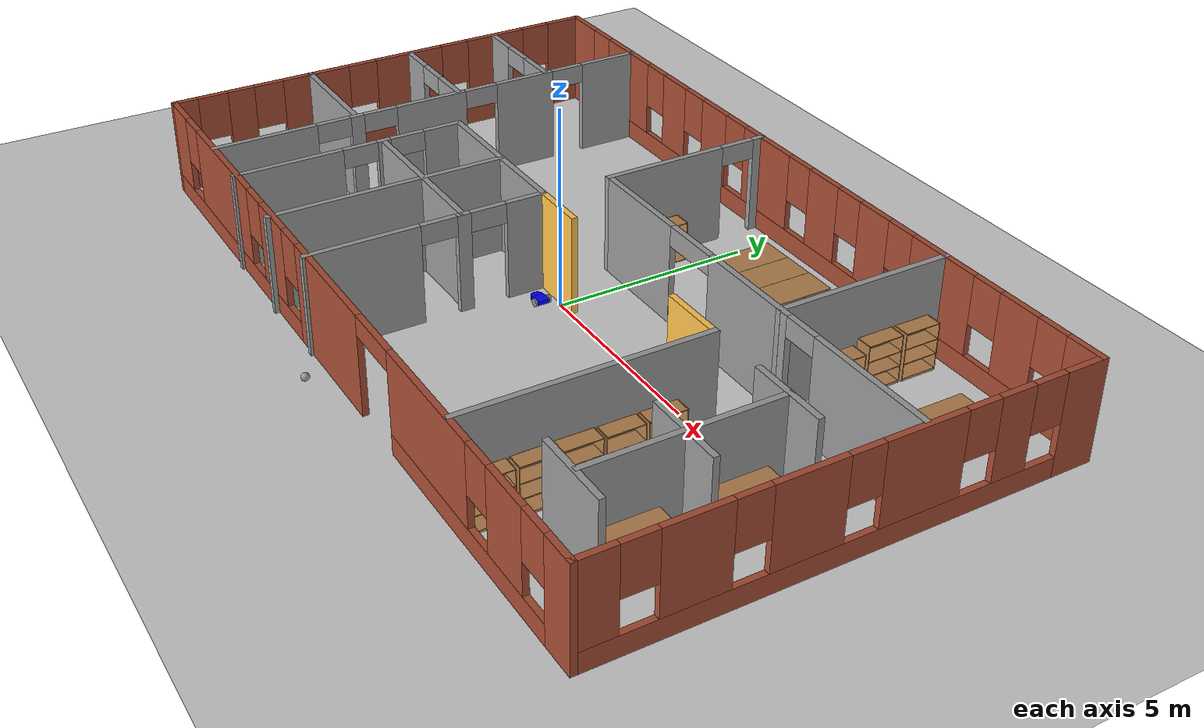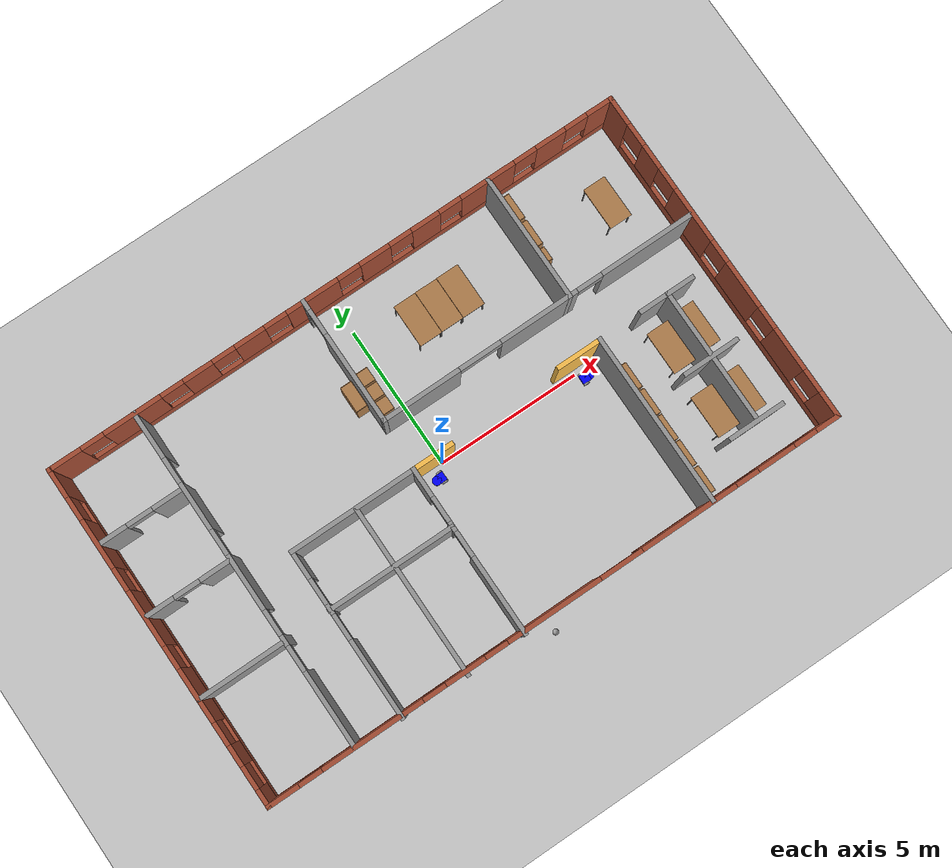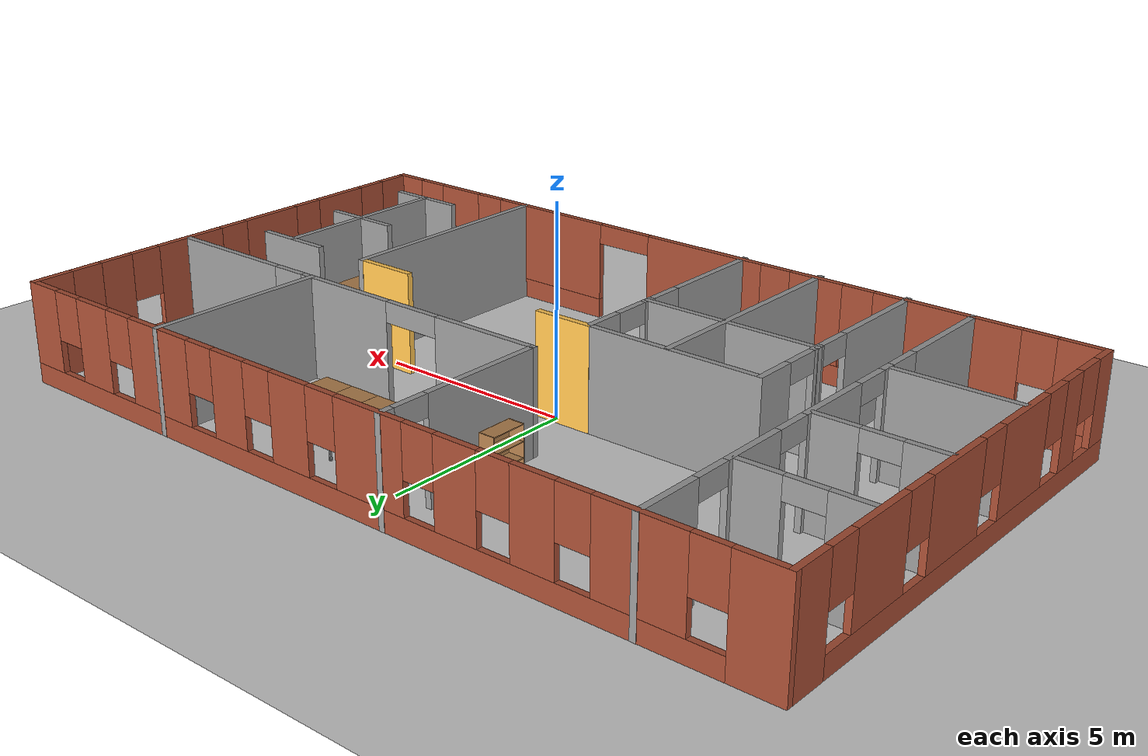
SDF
<sdf version="1.6">
 <world name="default">
  <plugin name="SimplePlugin" filename="libSimplePlugin.so"/>
  <light name="sun" type="directional">
   <pose>0 0 10 0 -0 0</pose>
   <diffuse>0.8 0.8 0.8 1</diffuse>
   <specular>0.2 0.2 0.2 1</specular>
   <attenuation>
    <range>1000</range>
    <constant>0.9</constant>
    <linear>0.01</linear>
    <quadratic>0.001</quadratic>
   </attenuation>
   <direction>-0.5 0.1 -0.9</direction>
  </light>
  <model name="ground_plane">
   <static>1</static>
   <link name="link">
    <collision name="collision">
     <geometry><plane><normal>0 0 1</normal><size>100 100</size></plane></geometry>
     <surface>
      <contact><collide_bitmask>65535</collide_bitmask></contact>
      <friction><ode><mu>100</mu><mu2>50</mu2></ode></friction>
     </surface>
    </collision>
    <visual name="visual">
     <cast_shadows>0</cast_shadows>
     <geometry><plane><normal>0 0 1</normal><size>100 100</size></plane></geometry>
     <material>
      <script><uri>file://media/materials/scripts/gazebo.material</uri><name>Gazebo/Grey</name></script>
     </material>
    </visual>
   </link>
  </model>
  <gravity>0 0 -9.8</gravity>
  <magnetic_field>6e-06 2.3e-05 -4.2e-05</magnetic_field>
  <atmosphere type="adiabatic"/>
  <physics name="default_physics" default="0" type="ode">
   <max_step_size>0.001</max_step_size>
   <real_time_factor>1</real_time_factor>
   <real_time_update_rate>1000</real_time_update_rate>
  </physics>
  <scene><ambient>0.4 0.4 0.4 1</ambient><background>0.7 0.7 0.7 1</background><shadows>1</shadows></scene>
  <spherical_coordinates>
   <surface_model>EARTH_WGS84</surface_model>
   <latitude_deg>0</latitude_deg>
   <longitude_deg>0</longitude_deg>
   <elevation>0</elevation>
   <heading_deg>0</heading_deg>
  </spherical_coordinates>
  <model name="model-02">
   <pose>0.22575 0.187769 0 0 -0 0</pose>
   <link name="Wall_0">
    <pose>-10.175 0.053057 0 0 0 -1.5708</pose>
    <visual name="Wall_0_Visual_0">
     <pose>-5.46659 0 1.25 0 -0 0</pose>
     <geometry><box><size>1.06682 0.15 2.5</size></box></geometry>
     <material>
      <script><uri>file://media/materials/scripts/gazebo.material</uri><name>Gazebo/Bricks</name></script>
      <ambient>1 1 1 1</ambient>
     </material>
     <meta><layer>0</layer></meta>
    </visual>
    <collision name="Wall_0_Collision_0">
     <geometry><box><size>1.06682 0.15 2.5</size></box></geometry>
     <pose>-5.46659 0 1.25 0 -0 0</pose>
    </collision>
    <visual name="Wall_0_Visual_1">
     <pose>0.53341 0 0.25 0 -0 0</pose>
     <geometry><box><size>10.9332 0.15 0.5</size></box></geometry>
     <material>
      <script><uri>file://media/materials/scripts/gazebo.material</uri><name>Gazebo/Bricks</name></script>
      <ambient>1 1 1 1</ambient>
     </material>
     <meta><layer>0</layer></meta>
    </visual>
    <collision name="Wall_0_Collision_1">
     <geometry><box><size>10.9332 0.15 0.5</size></box></geometry>
     <pose>0.53341 0 0.25 0 -0 0</pose>
    </collision>
    <visual name="Wall_0_Visual_2">
     <pose>-3.26711 0 1.5 0 -0 0</pose>
     <geometry><box><size>1.73215 0.15 2</size></box></geometry>
     <material>
      <script><uri>file://media/materials/scripts/gazebo.material</uri><name>Gazebo/Bricks</name></script>
      <ambient>1 1 1 1</ambient>
     </material>
     <meta><layer>0</layer></meta>
    </visual>
    <collision name="Wall_0_Collision_2">
     <geometry><box><size>1.73215 0.15 2</size></box></geometry>
     <pose>-3.26711 0 1.5 0 -0 0</pose>
    </collision>
    <visual name="Wall_0_Visual_3">
     <pose>-0.625092 0 1.5 0 -0 0</pose>
     <geometry><box><size>1.95188 0.15 2</size></box></geometry>
     <material>
      <script><uri>file://media/materials/scripts/gazebo.material</uri><name>Gazebo/Bricks</name></script>
      <ambient>1 1 1 1</ambient>
     </material>
     <meta><layer>0</layer></meta>
    </visual>
    <collision name="Wall_0_Collision_3">
     <geometry><box><size>1.95188 0.15 2</size></box></geometry>
     <pose>-0.625092 0 1.5 0 -0 0</pose>
    </collision>
    <visual name="Wall_0_Visual_4">
     <pose>2.08493 0 1.5 0 -0 0</pose>
     <geometry><box><size>1.86817 0.15 2</size></box></geometry>
     <material>
      <script><uri>file://media/materials/scripts/gazebo.material</uri><name>Gazebo/Bricks</name></script>
      <ambient>1 1 1 1</ambient>
     </material>
     <meta><layer>0</layer></meta>
    </visual>
    <collision name="Wall_0_Collision_4">
     <geometry><box><size>1.86817 0.15 2</size></box></geometry>
     <pose>2.08493 0 1.5 0 -0 0</pose>
    </collision>
    <visual name="Wall_0_Visual_5">
     <pose>4.17762 0 1.5 0 -0 0</pose>
     <geometry><box><size>0.717196 0.15 2</size></box></geometry>
     <material>
      <script><uri>file://media/materials/scripts/gazebo.material</uri><name>Gazebo/Bricks</name></script>
      <ambient>1 1 1 1</ambient>
     </material>
     <meta><layer>0</layer></meta>
    </visual>
    <collision name="Wall_0_Collision_5">
     <geometry><box><size>0.717196 0.15 2</size></box></geometry>
     <pose>4.17762 0 1.5 0 -0 0</pose>
    </collision>
    <visual name="Wall_0_Visual_6">
     <pose>5.66811 0 1.5 0 -0 0</pose>
     <geometry><box><size>0.663785 0.15 2</size></box></geometry>
     <material>
      <script><uri>file://media/materials/scripts/gazebo.material</uri><name>Gazebo/Bricks</name></script>
      <ambient>1 1 1 1</ambient>
     </material>
     <meta><layer>0</layer></meta>
    </visual>
    <collision name="Wall_0_Collision_6">
     <geometry><box><size>0.663785 0.15 2</size></box></geometry>
     <pose>5.66811 0 1.5 0 -0 0</pose>
    </collision>
    <visual name="Wall_0_Visual_7">
     <pose>-4.53318 0 1.9 0 -0 0</pose>
     <geometry><box><size>0.8 0.15 1.2</size></box></geometry>
     <material>
      <script><uri>file://media/materials/scripts/gazebo.material</uri><name>Gazebo/Bricks</name></script>
      <ambient>1 1 1 1</ambient>
     </material>
     <meta><layer>0</layer></meta>
    </visual>
    <collision name="Wall_0_Collision_7">
     <geometry><box><size>0.8 0.15 1.2</size></box></geometry>
     <pose>-4.53318 0 1.9 0 -0 0</pose>
    </collision>
    <visual name="Wall_0_Visual_8">
     <pose>-2.00103 0 1.9 0 -0 0</pose>
     <geometry><box><size>0.8 0.15 1.2</size></box></geometry>
     <material>
      <script><uri>file://media/materials/scripts/gazebo.material</uri><name>Gazebo/Bricks</name></script>
      <ambient>1 1 1 1</ambient>
     </material>
     <meta><layer>0</layer></meta>
    </visual>
    <collision name="Wall_0_Collision_8">
     <geometry><box><size>0.8 0.15 1.2</size></box></geometry>
     <pose>-2.00103 0 1.9 0 -0 0</pose>
    </collision>
    <visual name="Wall_0_Visual_9">
     <pose>0.750848 0 1.9 0 -0 0</pose>
     <geometry><box><size>0.8 0.15 1.2</size></box></geometry>
     <material>
      <script><uri>file://media/materials/scripts/gazebo.material</uri><name>Gazebo/Bricks</name></script>
      <ambient>1 1 1 1</ambient>
     </material>
     <meta><layer>0</layer></meta>
    </visual>
    <collision name="Wall_0_Collision_9">
     <geometry><box><size>0.8 0.15 1.2</size></box></geometry>
     <pose>0.750848 0 1.9 0 -0 0</pose>
    </collision>
    <visual name="Wall_0_Visual_10">
     <pose>3.41902 0 1.9 0 -0 0</pose>
     <geometry><box><size>0.8 0.15 1.2</size></box></geometry>
     <material>
      <script><uri>file://media/materials/scripts/gazebo.material</uri><name>Gazebo/Bricks</name></script>
      <ambient>1 1 1 1</ambient>
     </material>
     <meta><layer>0</layer></meta>
    </visual>
    <collision name="Wall_0_Collision_10">
     <geometry><box><size>0.8 0.15 1.2</size></box></geometry>
     <pose>3.41902 0 1.9 0 -0 0</pose>
    </collision>
    <visual name="Wall_0_Visual_11">
     <pose>4.93621 0 1.9 0 -0 0</pose>
     <geometry><box><size>0.8 0.15 1.2</size></box></geometry>
     <material>
      <script><uri>file://media/materials/scripts/gazebo.material</uri><name>Gazebo/Bricks</name></script>
      <ambient>1 1 1 1</ambient>
     </material>
     <meta><layer>0</layer></meta>
    </visual>
    <collision name="Wall_0_Collision_11">
     <geometry><box><size>0.8 0.15 1.2</size></box></geometry>
     <pose>4.93621 0 1.9 0 -0 0</pose>
    </collision>
   </link>
   <link name="Wall_10">
    <pose>-8.66526 3.2872 0 0 -0 3.14159</pose>
    <visual name="Wall_10_Visual_0">
     <pose>-0.949963 0 1.25 0 -0 0</pose>
     <geometry><box><size>1.10007 0.15 2.5</size></box></geometry>
     <material>
      <script><uri>file://media/materials/scripts/gazebo.material</uri><name>Gazebo/Grey</name></script>
      <ambient>1 1 1 1</ambient>
     </material>
     <meta><layer>0</layer></meta>
    </visual>
    <collision name="Wall_10_Collision_0">
     <geometry><box><size>1.10007 0.15 2.5</size></box></geometry>
     <pose>-0.949963 0 1.25 0 -0 0</pose>
    </collision>
    <visual name="Wall_10_Visual_1">
     <pose>1.00004 0 1.25 0 -0 0</pose>
     <geometry><box><size>0.999926 0.15 2.5</size></box></geometry>
     <material>
      <script><uri>file://media/materials/scripts/gazebo.material</uri><name>Gazebo/Grey</name></script>
      <ambient>1 1 1 1</ambient>
     </material>
     <meta><layer>0</layer></meta>
    </visual>
    <collision name="Wall_10_Collision_1">
     <geometry><box><size>0.999926 0.15 2.5</size></box></geometry>
     <pose>1.00004 0 1.25 0 -0 0</pose>
    </collision>
    <visual name="Wall_10_Visual_2">
     <pose>0.050074 0 2.25 0 -0 0</pose>
     <geometry><box><size>0.9 0.15 0.5</size></box></geometry>
     <material>
      <script><uri>file://media/materials/scripts/gazebo.material</uri><name>Gazebo/Grey</name></script>
      <ambient>1 1 1 1</ambient>
     </material>
     <meta><layer>0</layer></meta>
    </visual>
    <collision name="Wall_10_Collision_2">
     <geometry><box><size>0.9 0.15 0.5</size></box></geometry>
     <pose>0.050074 0 2.25 0 -0 0</pose>
    </collision>
   </link>
   <link name="Wall_12">
    <pose>-8.66526 0.722887 0 0 -0 3.14159</pose>
    <visual name="Wall_12_Visual_0">
     <pose>-0.949963 0 1.25 0 -0 0</pose>
     <geometry><box><size>1.10007 0.15 2.5</size></box></geometry>
     <material>
      <script><uri>file://media/materials/scripts/gazebo.material</uri><name>Gazebo/Grey</name></script>
      <ambient>1 1 1 1</ambient>
     </material>
     <meta><layer>0</layer></meta>
    </visual>
    <collision name="Wall_12_Collision_0">
     <geometry><box><size>1.10007 0.15 2.5</size></box></geometry>
     <pose>-0.949963 0 1.25 0 -0 0</pose>
    </collision>
    <visual name="Wall_12_Visual_1">
     <pose>1.00004 0 1.25 0 -0 0</pose>
     <geometry><box><size>0.999926 0.15 2.5</size></box></geometry>
     <material>
      <script><uri>file://media/materials/scripts/gazebo.material</uri><name>Gazebo/Grey</name></script>
      <ambient>1 1 1 1</ambient>
     </material>
     <meta><layer>0</layer></meta>
    </visual>
    <collision name="Wall_12_Collision_1">
     <geometry><box><size>0.999926 0.15 2.5</size></box></geometry>
     <pose>1.00004 0 1.25 0 -0 0</pose>
    </collision>
    <visual name="Wall_12_Visual_2">
     <pose>0.050074 0 2.25 0 -0 0</pose>
     <geometry><box><size>0.9 0.15 0.5</size></box></geometry>
     <material>
      <script><uri>file://media/materials/scripts/gazebo.material</uri><name>Gazebo/Grey</name></script>
      <ambient>1 1 1 1</ambient>
     </material>
     <meta><layer>0</layer></meta>
    </visual>
    <collision name="Wall_12_Collision_2">
     <geometry><box><size>0.9 0.15 0.5</size></box></geometry>
     <pose>0.050074 0 2.25 0 -0 0</pose>
    </collision>
   </link>
   <link name="Wall_14">
    <collision name="Wall_14_Collision">
     <geometry><box><size>3 0.15 2.5</size></box></geometry>
     <pose>0 0 1.25 0 -0 0</pose>
    </collision>
    <visual name="Wall_14_Visual">
     <pose>0 0 1.25 0 -0 0</pose>
     <geometry><box><size>3 0.15 2.5</size></box></geometry>
     <material>
      <script><uri>file://media/materials/scripts/gazebo.material</uri><name>Gazebo/Grey</name></script>
      <ambient>1 1 1 1</ambient>
     </material>
     <meta><layer>0</layer></meta>
    </visual>
    <pose>-8.719 -2.16168 0 0 -0 3.14159</pose>
   </link>
   <link name="Wall_2">
    <pose>0 5.97806 0 0 -0 0</pose>
    <visual name="Wall_2_Visual_0">
     <pose>-9.65114 0 1.25 0 -0 0</pose>
     <geometry><box><size>1.19772 0.15 2.5</size></box></geometry>
     <material>
      <script><uri>file://media/materials/scripts/gazebo.material</uri><name>Gazebo/Bricks</name></script>
      <ambient>1 1 1 1</ambient>
     </material>
     <meta><layer>0</layer></meta>
    </visual>
    <collision name="Wall_2_Collision_0">
     <geometry><box><size>1.19772 0.15 2.5</size></box></geometry>
     <pose>-9.65114 0 1.25 0 -0 0</pose>
    </collision>
    <visual name="Wall_2_Visual_1">
     <pose>0.598862 0 0.25 0 -0 0</pose>
     <geometry><box><size>19.3023 0.15 0.5</size></box></geometry>
     <material>
      <script><uri>file://media/materials/scripts/gazebo.material</uri><name>Gazebo/Bricks</name></script>
      <ambient>1 1 1 1</ambient>
     </material>
     <meta><layer>0</layer></meta>
    </visual>
    <collision name="Wall_2_Collision_1">
     <geometry><box><size>19.3023 0.15 0.5</size></box></geometry>
     <pose>0.598862 0 0.25 0 -0 0</pose>
    </collision>
    <visual name="Wall_2_Visual_2">
     <pose>-7.23766 0 1.5 0 -0 0</pose>
     <geometry><box><size>2.02923 0.15 2</size></box></geometry>
     <material>
      <script><uri>file://media/materials/scripts/gazebo.material</uri><name>Gazebo/Bricks</name></script>
      <ambient>1 1 1 1</ambient>
     </material>
     <meta><layer>0</layer></meta>
    </visual>
    <collision name="Wall_2_Collision_2">
     <geometry><box><size>2.02923 0.15 2</size></box></geometry>
     <pose>-7.23766 0 1.5 0 -0 0</pose>
    </collision>
    <visual name="Wall_2_Visual_3">
     <pose>-4.90335 0 1.5 0 -0 0</pose>
     <geometry><box><size>1.03939 0.15 2</size></box></geometry>
     <material>
      <script><uri>file://media/materials/scripts/gazebo.material</uri><name>Gazebo/Bricks</name></script>
      <ambient>1 1 1 1</ambient>
     </material>
     <meta><layer>0</layer></meta>
    </visual>
    <collision name="Wall_2_Collision_3">
     <geometry><box><size>1.03939 0.15 2</size></box></geometry>
     <pose>-4.90335 0 1.5 0 -0 0</pose>
    </collision>
    <visual name="Wall_2_Visual_4">
     <pose>-3.05186 0 1.5 0 -0 0</pose>
     <geometry><box><size>1.0636 0.15 2</size></box></geometry>
     <material>
      <script><uri>file://media/materials/scripts/gazebo.material</uri><name>Gazebo/Bricks</name></script>
      <ambient>1 1 1 1</ambient>
     </material>
     <meta><layer>0</layer></meta>
    </visual>
    <collision name="Wall_2_Collision_4">
     <geometry><box><size>1.0636 0.15 2</size></box></geometry>
     <pose>-3.05186 0 1.5 0 -0 0</pose>
    </collision>
    <visual name="Wall_2_Visual_5">
     <pose>-0.796768 0 1.5 0 -0 0</pose>
     <geometry><box><size>1.84658 0.15 2</size></box></geometry>
     <material>
      <script><uri>file://media/materials/scripts/gazebo.material</uri><name>Gazebo/Bricks</name></script>
      <ambient>1 1 1 1</ambient>
     </material>
     <meta><layer>0</layer></meta>
    </visual>
    <collision name="Wall_2_Collision_5">
     <geometry><box><size>1.84658 0.15 2</size></box></geometry>
     <pose>-0.796768 0 1.5 0 -0 0</pose>
    </collision>
    <visual name="Wall_2_Visual_6">
     <pose>1.4675 0 1.5 0 -0 0</pose>
     <geometry><box><size>1.08195 0.15 2</size></box></geometry>
     <material>
      <script><uri>file://media/materials/scripts/gazebo.material</uri><name>Gazebo/Bricks</name></script>
      <ambient>1 1 1 1</ambient>
     </material>
     <meta><layer>0</layer></meta>
    </visual>
    <collision name="Wall_2_Collision_6">
     <geometry><box><size>1.08195 0.15 2</size></box></geometry>
     <pose>1.4675 0 1.5 0 -0 0</pose>
    </collision>
    <visual name="Wall_2_Visual_7">
     <pose>3.31485 0 1.5 0 -0 0</pose>
     <geometry><box><size>1.01276 0.15 2</size></box></geometry>
     <material>
      <script><uri>file://media/materials/scripts/gazebo.material</uri><name>Gazebo/Bricks</name></script>
      <ambient>1 1 1 1</ambient>
     </material>
     <meta><layer>0</layer></meta>
    </visual>
    <collision name="Wall_2_Collision_7">
     <geometry><box><size>1.01276 0.15 2</size></box></geometry>
     <pose>3.31485 0 1.5 0 -0 0</pose>
    </collision>
    <visual name="Wall_2_Visual_8">
     <pose>5.60502 0 1.5 0 -0 0</pose>
     <geometry><box><size>1.96757 0.15 2</size></box></geometry>
     <material>
      <script><uri>file://media/materials/scripts/gazebo.material</uri><name>Gazebo/Bricks</name></script>
      <ambient>1 1 1 1</ambient>
     </material>
     <meta><layer>0</layer></meta>
    </visual>
    <collision name="Wall_2_Collision_8">
     <geometry><box><size>1.96757 0.15 2</size></box></geometry>
     <pose>5.60502 0 1.5 0 -0 0</pose>
    </collision>
    <visual name="Wall_2_Visual_9">
     <pose>7.92978 0 1.5 0 -0 0</pose>
     <geometry><box><size>1.08195 0.15 2</size></box></geometry>
     <material>
      <script><uri>file://media/materials/scripts/gazebo.material</uri><name>Gazebo/Bricks</name></script>
      <ambient>1 1 1 1</ambient>
     </material>
     <meta><layer>0</layer></meta>
    </visual>
    <collision name="Wall_2_Collision_9">
     <geometry><box><size>1.08195 0.15 2</size></box></geometry>
     <pose>7.92978 0 1.5 0 -0 0</pose>
    </collision>
    <visual name="Wall_2_Visual_10">
     <pose>9.76038 0 1.5 0 -0 0</pose>
     <geometry><box><size>0.979241 0.15 2</size></box></geometry>
     <material>
      <script><uri>file://media/materials/scripts/gazebo.material</uri><name>Gazebo/Bricks</name></script>
      <ambient>1 1 1 1</ambient>
     </material>
     <meta><layer>0</layer></meta>
    </visual>
    <collision name="Wall_2_Collision_10">
     <geometry><box><size>0.979241 0.15 2</size></box></geometry>
     <pose>9.76038 0 1.5 0 -0 0</pose>
    </collision>
    <visual name="Wall_2_Visual_11">
     <pose>-8.65228 0 1.9 0 -0 0</pose>
     <geometry><box><size>0.8 0.15 1.2</size></box></geometry>
     <material>
      <script><uri>file://media/materials/scripts/gazebo.material</uri><name>Gazebo/Bricks</name></script>
      <ambient>1 1 1 1</ambient>
     </material>
     <meta><layer>0</layer></meta>
    </visual>
    <collision name="Wall_2_Collision_11">
     <geometry><box><size>0.8 0.15 1.2</size></box></geometry>
     <pose>-8.65228 0 1.9 0 -0 0</pose>
    </collision>
    <visual name="Wall_2_Visual_12">
     <pose>-5.82304 0 1.9 0 -0 0</pose>
     <geometry><box><size>0.8 0.15 1.2</size></box></geometry>
     <material>
      <script><uri>file://media/materials/scripts/gazebo.material</uri><name>Gazebo/Bricks</name></script>
      <ambient>1 1 1 1</ambient>
     </material>
     <meta><layer>0</layer></meta>
    </visual>
    <collision name="Wall_2_Collision_12">
     <geometry><box><size>0.8 0.15 1.2</size></box></geometry>
     <pose>-5.82304 0 1.9 0 -0 0</pose>
    </collision>
    <visual name="Wall_2_Visual_13">
     <pose>-3.98365 0 1.9 0 -0 0</pose>
     <geometry><box><size>0.8 0.15 1.2</size></box></geometry>
     <material>
      <script><uri>file://media/materials/scripts/gazebo.material</uri><name>Gazebo/Bricks</name></script>
      <ambient>1 1 1 1</ambient>
     </material>
     <meta><layer>0</layer></meta>
    </visual>
    <collision name="Wall_2_Collision_13">
     <geometry><box><size>0.8 0.15 1.2</size></box></geometry>
     <pose>-3.98365 0 1.9 0 -0 0</pose>
    </collision>
    <visual name="Wall_2_Visual_14">
     <pose>-2.12006 0 1.9 0 -0 0</pose>
     <geometry><box><size>0.8 0.15 1.2</size></box></geometry>
     <material>
      <script><uri>file://media/materials/scripts/gazebo.material</uri><name>Gazebo/Bricks</name></script>
      <ambient>1 1 1 1</ambient>
     </material>
     <meta><layer>0</layer></meta>
    </visual>
    <collision name="Wall_2_Collision_14">
     <geometry><box><size>0.8 0.15 1.2</size></box></geometry>
     <pose>-2.12006 0 1.9 0 -0 0</pose>
    </collision>
    <visual name="Wall_2_Visual_15">
     <pose>0.526522 0 1.9 0 -0 0</pose>
     <geometry><box><size>0.8 0.15 1.2</size></box></geometry>
     <material>
      <script><uri>file://media/materials/scripts/gazebo.material</uri><name>Gazebo/Bricks</name></script>
      <ambient>1 1 1 1</ambient>
     </material>
     <meta><layer>0</layer></meta>
    </visual>
    <collision name="Wall_2_Collision_15">
     <geometry><box><size>0.8 0.15 1.2</size></box></geometry>
     <pose>0.526522 0 1.9 0 -0 0</pose>
    </collision>
    <visual name="Wall_2_Visual_16">
     <pose>2.40847 0 1.9 0 -0 0</pose>
     <geometry><box><size>0.8 0.15 1.2</size></box></geometry>
     <material>
      <script><uri>file://media/materials/scripts/gazebo.material</uri><name>Gazebo/Bricks</name></script>
      <ambient>1 1 1 1</ambient>
     </material>
     <meta><layer>0</layer></meta>
    </visual>
    <collision name="Wall_2_Collision_16">
     <geometry><box><size>0.8 0.15 1.2</size></box></geometry>
     <pose>2.40847 0 1.9 0 -0 0</pose>
    </collision>
    <visual name="Wall_2_Visual_17">
     <pose>4.22123 0 1.9 0 -0 0</pose>
     <geometry><box><size>0.8 0.15 1.2</size></box></geometry>
     <material>
      <script><uri>file://media/materials/scripts/gazebo.material</uri><name>Gazebo/Bricks</name></script>
      <ambient>1 1 1 1</ambient>
     </material>
     <meta><layer>0</layer></meta>
    </visual>
    <collision name="Wall_2_Collision_17">
     <geometry><box><size>0.8 0.15 1.2</size></box></geometry>
     <pose>4.22123 0 1.9 0 -0 0</pose>
    </collision>
    <visual name="Wall_2_Visual_18">
     <pose>6.98881 0 1.9 0 -0 0</pose>
     <geometry><box><size>0.8 0.15 1.2</size></box></geometry>
     <material>
      <script><uri>file://media/materials/scripts/gazebo.material</uri><name>Gazebo/Bricks</name></script>
      <ambient>1 1 1 1</ambient>
     </material>
     <meta><layer>0</layer></meta>
    </visual>
    <collision name="Wall_2_Collision_18">
     <geometry><box><size>0.8 0.15 1.2</size></box></geometry>
     <pose>6.98881 0 1.9 0 -0 0</pose>
    </collision>
    <visual name="Wall_2_Visual_19">
     <pose>8.87076 0 1.9 0 -0 0</pose>
     <geometry><box><size>0.8 0.15 1.2</size></box></geometry>
     <material>
      <script><uri>file://media/materials/scripts/gazebo.material</uri><name>Gazebo/Bricks</name></script>
      <ambient>1 1 1 1</ambient>
     </material>
     <meta><layer>0</layer></meta>
    </visual>
    <collision name="Wall_2_Collision_19">
     <geometry><box><size>0.8 0.15 1.2</size></box></geometry>
     <pose>8.87076 0 1.9 0 -0 0</pose>
    </collision>
   </link>
   <link name="Wall_26">
    <pose>-1.10403 3.80806 0 0 -0 1.57081</pose>
    <visual name="Wall_26_Visual_0">
     <pose>-0.640492 0 1.25 0 -0 0</pose>
     <geometry><box><size>3.21902 0.15 2.5</size></box></geometry>
     <material>
      <script><uri>file://media/materials/scripts/gazebo.material</uri><name>Gazebo/Grey</name></script>
      <ambient>1 1 1 1</ambient>
     </material>
     <meta><layer>0</layer></meta>
    </visual>
    <collision name="Wall_26_Collision_0">
     <geometry><box><size>3.21902 0.15 2.5</size></box></geometry>
     <pose>-0.640492 0 1.25 0 -0 0</pose>
    </collision>
    <visual name="Wall_26_Visual_1">
     <pose>2.05951 0 1.25 0 -0 0</pose>
     <geometry><box><size>0.380984 0.15 2.5</size></box></geometry>
     <material>
      <script><uri>file://media/materials/scripts/gazebo.material</uri><name>Gazebo/Grey</name></script>
      <ambient>1 1 1 1</ambient>
     </material>
     <meta><layer>0</layer></meta>
    </visual>
    <collision name="Wall_26_Collision_1">
     <geometry><box><size>0.380984 0.15 2.5</size></box></geometry>
     <pose>2.05951 0 1.25 0 -0 0</pose>
    </collision>
    <visual name="Wall_26_Visual_2">
     <pose>1.41902 0 2.25 0 -0 0</pose>
     <geometry><box><size>0.9 0.15 0.5</size></box></geometry>
     <material>
      <script><uri>file://media/materials/scripts/gazebo.material</uri><name>Gazebo/Grey</name></script>
      <ambient>1 1 1 1</ambient>
     </material>
     <meta><layer>0</layer></meta>
    </visual>
    <collision name="Wall_26_Collision_2">
     <geometry><box><size>0.9 0.15 0.5</size></box></geometry>
     <pose>1.41902 0 2.25 0 -0 0</pose>
    </collision>
   </link>
   <link name="Wall_28">
    <pose>4.4795 1.63306 0 0 -0 0</pose>
    <visual name="Wall_28_Visual_0">
     <pose>-4.25709 0 1.25 0 -0 0</pose>
     <geometry><box><size>2.80283 0.15 2.5</size></box></geometry>
     <material>
      <script><uri>file://media/materials/scripts/gazebo.material</uri><name>Gazebo/Grey</name></script>
      <ambient>1 1 1 1</ambient>
     </material>
     <meta><layer>0</layer></meta>
    </visual>
    <collision name="Wall_28_Collision_0">
     <geometry><box><size>2.80283 0.15 2.5</size></box></geometry>
     <pose>-4.25709 0 1.25 0 -0 0</pose>
    </collision>
    <visual name="Wall_28_Visual_1">
     <pose>0.041694 0 1.25 0 -0 0</pose>
     <geometry><box><size>2.79473 0.15 2.5</size></box></geometry>
     <material>
      <script><uri>file://media/materials/scripts/gazebo.material</uri><name>Gazebo/Grey</name></script>
      <ambient>1 1 1 1</ambient>
     </material>
     <meta><layer>0</layer></meta>
    </visual>
    <collision name="Wall_28_Collision_1">
     <geometry><box><size>2.79473 0.15 2.5</size></box></geometry>
     <pose>0.041694 0 1.25 0 -0 0</pose>
    </collision>
    <visual name="Wall_28_Visual_2">
     <pose>3.99878 0 1.25 0 -0 0</pose>
     <geometry><box><size>3.31944 0.15 2.5</size></box></geometry>
     <material>
      <script><uri>file://media/materials/scripts/gazebo.material</uri><name>Gazebo/Grey</name></script>
      <ambient>1 1 1 1</ambient>
     </material>
     <meta><layer>0</layer></meta>
    </visual>
    <collision name="Wall_28_Collision_2">
     <geometry><box><size>3.31944 0.15 2.5</size></box></geometry>
     <pose>3.99878 0 1.25 0 -0 0</pose>
    </collision>
    <visual name="Wall_28_Visual_3">
     <pose>-2.10567 0 2.25 0 -0 0</pose>
     <geometry><box><size>1.5 0.15 0.5</size></box></geometry>
     <material>
      <script><uri>file://media/materials/scripts/gazebo.material</uri><name>Gazebo/Grey</name></script>
      <ambient>1 1 1 1</ambient>
     </material>
     <meta><layer>0</layer></meta>
    </visual>
    <collision name="Wall_28_Collision_3">
     <geometry><box><size>1.5 0.15 0.5</size></box></geometry>
     <pose>-2.10567 0 2.25 0 -0 0</pose>
    </collision>
    <visual name="Wall_28_Visual_4">
     <pose>1.88906 0 2.25 0 -0 0</pose>
     <geometry><box><size>0.9 0.15 0.5</size></box></geometry>
     <material>
      <script><uri>file://media/materials/scripts/gazebo.material</uri><name>Gazebo/Grey</name></script>
      <ambient>1 1 1 1</ambient>
     </material>
     <meta><layer>0</layer></meta>
    </visual>
    <collision name="Wall_28_Collision_4">
     <geometry><box><size>0.9 0.15 0.5</size></box></geometry>
     <pose>1.88906 0 2.25 0 -0 0</pose>
    </collision>
   </link>
   <link name="Wall_3">
    <pose>10.175 0.053057 0 0 0 -1.5708</pose>
    <visual name="Wall_3_Visual_0">
     <pose>-5.47727 0 1.25 0 -0 0</pose>
     <geometry><box><size>1.04546 0.15 2.5</size></box></geometry>
     <material>
      <script><uri>file://media/materials/scripts/gazebo.material</uri><name>Gazebo/Bricks</name></script>
      <ambient>1 1 1 1</ambient>
     </material>
     <meta><layer>0</layer></meta>
    </visual>
    <collision name="Wall_3_Collision_0">
     <geometry><box><size>1.04546 0.15 2.5</size></box></geometry>
     <pose>-5.47727 0 1.25 0 -0 0</pose>
    </collision>
    <visual name="Wall_3_Visual_1">
     <pose>0.522727 0 0.25 0 -0 0</pose>
     <geometry><box><size>10.9545 0.15 0.5</size></box></geometry>
     <material>
      <script><uri>file://media/materials/scripts/gazebo.material</uri><name>Gazebo/Bricks</name></script>
      <ambient>1 1 1 1</ambient>
     </material>
     <meta><layer>0</layer></meta>
    </visual>
    <collision name="Wall_3_Collision_1">
     <geometry><box><size>10.9545 0.15 0.5</size></box></geometry>
     <pose>0.522727 0 0.25 0 -0 0</pose>
    </collision>
    <visual name="Wall_3_Visual_2">
     <pose>-3.72427 0 1.5 0 -0 0</pose>
     <geometry><box><size>0.860545 0.15 2</size></box></geometry>
     <material>
      <script><uri>file://media/materials/scripts/gazebo.material</uri><name>Gazebo/Bricks</name></script>
      <ambient>1 1 1 1</ambient>
     </material>
     <meta><layer>0</layer></meta>
    </visual>
    <collision name="Wall_3_Collision_2">
     <geometry><box><size>0.860545 0.15 2</size></box></geometry>
     <pose>-3.72427 0 1.5 0 -0 0</pose>
    </collision>
    <visual name="Wall_3_Visual_3">
     <pose>-1.52574 0 1.5 0 -0 0</pose>
     <geometry><box><size>1.93653 0.15 2</size></box></geometry>
     <material>
      <script><uri>file://media/materials/scripts/gazebo.material</uri><name>Gazebo/Bricks</name></script>
      <ambient>1 1 1 1</ambient>
     </material>
     <meta><layer>0</layer></meta>
    </visual>
    <collision name="Wall_3_Collision_3">
     <geometry><box><size>1.93653 0.15 2</size></box></geometry>
     <pose>-1.52574 0 1.5 0 -0 0</pose>
    </collision>
    <visual name="Wall_3_Visual_4">
     <pose>1.0759 0 1.5 0 -0 0</pose>
     <geometry><box><size>1.66675 0.15 2</size></box></geometry>
     <material>
      <script><uri>file://media/materials/scripts/gazebo.material</uri><name>Gazebo/Bricks</name></script>
      <ambient>1 1 1 1</ambient>
     </material>
     <meta><layer>0</layer></meta>
    </visual>
    <collision name="Wall_3_Collision_4">
     <geometry><box><size>1.66675 0.15 2</size></box></geometry>
     <pose>1.0759 0 1.5 0 -0 0</pose>
    </collision>
    <visual name="Wall_3_Visual_5">
     <pose>3.47046 0 1.5 0 -0 0</pose>
     <geometry><box><size>1.52236 0.15 2</size></box></geometry>
     <material>
      <script><uri>file://media/materials/scripts/gazebo.material</uri><name>Gazebo/Bricks</name></script>
      <ambient>1 1 1 1</ambient>
     </material>
     <meta><layer>0</layer></meta>
    </visual>
    <collision name="Wall_3_Collision_5">
     <geometry><box><size>1.52236 0.15 2</size></box></geometry>
     <pose>3.47046 0 1.5 0 -0 0</pose>
    </collision>
    <visual name="Wall_3_Visual_6">
     <pose>5.51582 0 1.5 0 -0 0</pose>
     <geometry><box><size>0.968366 0.15 2</size></box></geometry>
     <material>
      <script><uri>file://media/materials/scripts/gazebo.material</uri><name>Gazebo/Bricks</name></script>
      <ambient>1 1 1 1</ambient>
     </material>
     <meta><layer>0</layer></meta>
    </visual>
    <collision name="Wall_3_Collision_6">
     <geometry><box><size>0.968366 0.15 2</size></box></geometry>
     <pose>5.51582 0 1.5 0 -0 0</pose>
    </collision>
    <visual name="Wall_3_Visual_7">
     <pose>-4.55455 0 1.9 0 -0 0</pose>
     <geometry><box><size>0.8 0.15 1.2</size></box></geometry>
     <material>
      <script><uri>file://media/materials/scripts/gazebo.material</uri><name>Gazebo/Bricks</name></script>
      <ambient>1 1 1 1</ambient>
     </material>
     <meta><layer>0</layer></meta>
    </visual>
    <collision name="Wall_3_Collision_7">
     <geometry><box><size>0.8 0.15 1.2</size></box></geometry>
     <pose>-4.55455 0 1.9 0 -0 0</pose>
    </collision>
    <visual name="Wall_3_Visual_8">
     <pose>-2.894 0 1.9 0 -0 0</pose>
     <geometry><box><size>0.8 0.15 1.2</size></box></geometry>
     <material>
      <script><uri>file://media/materials/scripts/gazebo.material</uri><name>Gazebo/Bricks</name></script>
      <ambient>1 1 1 1</ambient>
     </material>
     <meta><layer>0</layer></meta>
    </visual>
    <collision name="Wall_3_Collision_8">
     <geometry><box><size>0.8 0.15 1.2</size></box></geometry>
     <pose>-2.894 0 1.9 0 -0 0</pose>
    </collision>
    <visual name="Wall_3_Visual_9">
     <pose>-0.157473 0 1.9 0 -0 0</pose>
     <geometry><box><size>0.8 0.15 1.2</size></box></geometry>
     <material>
      <script><uri>file://media/materials/scripts/gazebo.material</uri><name>Gazebo/Bricks</name></script>
      <ambient>1 1 1 1</ambient>
     </material>
     <meta><layer>0</layer></meta>
    </visual>
    <collision name="Wall_3_Collision_9">
     <geometry><box><size>0.8 0.15 1.2</size></box></geometry>
     <pose>-0.157473 0 1.9 0 -0 0</pose>
    </collision>
    <visual name="Wall_3_Visual_10">
     <pose>2.30928 0 1.9 0 -0 0</pose>
     <geometry><box><size>0.8 0.15 1.2</size></box></geometry>
     <material>
      <script><uri>file://media/materials/scripts/gazebo.material</uri><name>Gazebo/Bricks</name></script>
      <ambient>1 1 1 1</ambient>
     </material>
     <meta><layer>0</layer></meta>
    </visual>
    <collision name="Wall_3_Collision_10">
     <geometry><box><size>0.8 0.15 1.2</size></box></geometry>
     <pose>2.30928 0 1.9 0 -0 0</pose>
    </collision>
    <visual name="Wall_3_Visual_11">
     <pose>4.63163 0 1.9 0 -0 0</pose>
     <geometry><box><size>0.8 0.15 1.2</size></box></geometry>
     <material>
      <script><uri>file://media/materials/scripts/gazebo.material</uri><name>Gazebo/Bricks</name></script>
      <ambient>1 1 1 1</ambient>
     </material>
     <meta><layer>0</layer></meta>
    </visual>
    <collision name="Wall_3_Collision_11">
     <geometry><box><size>0.8 0.15 1.2</size></box></geometry>
     <pose>4.63163 0 1.9 0 -0 0</pose>
    </collision>
   </link>
   <link name="Wall_30">
    <collision name="Wall_30_Collision">
     <geometry><box><size>4.5 0.15 2.5</size></box></geometry>
     <pose>0 0 1.25 0 -0 0</pose>
    </collision>
    <visual name="Wall_30_Visual">
     <pose>0 0 1.25 0 -0 0</pose>
     <geometry><box><size>4.5 0.15 2.5</size></box></geometry>
     <material>
      <script><uri>file://media/materials/scripts/gazebo.material</uri><name>Gazebo/Grey</name></script>
      <ambient>1 1 1 1</ambient>
     </material>
     <meta><layer>0</layer></meta>
    </visual>
    <pose>5.63149 3.80627 0 0 -0 1.5708</pose>
   </link>
   <link name="Wall_32">
    <collision name="Wall_32_Collision">
     <geometry><box><size>6 0.15 2.5</size></box></geometry>
     <pose>0 0 1.25 0 -0 0</pose>
    </collision>
    <visual name="Wall_32_Visual">
     <pose>0 0 1.25 0 -0 0</pose>
     <geometry><box><size>6 0.15 2.5</size></box></geometry>
     <material>
      <script><uri>file://media/materials/scripts/gazebo.material</uri><name>Gazebo/Grey</name></script>
      <ambient>1 1 1 1</ambient>
     </material>
     <meta><layer>0</layer></meta>
    </visual>
    <pose>5.62609 -2.90654 0 0 -0 1.5708</pose>
   </link>
   <link name="Wall_34">
    <pose>-5.54817 -3.01582 0 0 -0 1.5708</pose>
    <visual name="Wall_34_Visual_0">
     <pose>-1.59858 0 1.25 0 -0 0</pose>
     <geometry><box><size>2.80283 0.15 2.5</size></box></geometry>
     <material>
      <script><uri>file://media/materials/scripts/gazebo.material</uri><name>Gazebo/Grey</name></script>
      <ambient>1 1 1 1</ambient>
     </material>
     <meta><layer>0</layer></meta>
    </visual>
    <collision name="Wall_34_Collision_0">
     <geometry><box><size>2.80283 0.15 2.5</size></box></geometry>
     <pose>-1.59858 0 1.25 0 -0 0</pose>
    </collision>
    <visual name="Wall_34_Visual_1">
     <pose>0.878194 0 1.25 0 -0 0</pose>
     <geometry><box><size>0.350724 0.15 2.5</size></box></geometry>
     <material>
      <script><uri>file://media/materials/scripts/gazebo.material</uri><name>Gazebo/Grey</name></script>
      <ambient>1 1 1 1</ambient>
     </material>
     <meta><layer>0</layer></meta>
    </visual>
    <collision name="Wall_34_Collision_1">
     <geometry><box><size>0.350724 0.15 2.5</size></box></geometry>
     <pose>0.878194 0 1.25 0 -0 0</pose>
    </collision>
    <visual name="Wall_34_Visual_2">
     <pose>2.47678 0 1.25 0 -0 0</pose>
     <geometry><box><size>1.04644 0.15 2.5</size></box></geometry>
     <material>
      <script><uri>file://media/materials/scripts/gazebo.material</uri><name>Gazebo/Grey</name></script>
      <ambient>1 1 1 1</ambient>
     </material>
     <meta><layer>0</layer></meta>
    </visual>
    <collision name="Wall_34_Collision_2">
     <geometry><box><size>1.04644 0.15 2.5</size></box></geometry>
     <pose>2.47678 0 1.25 0 -0 0</pose>
    </collision>
    <visual name="Wall_34_Visual_3">
     <pose>0.252832 0 2.25 0 -0 0</pose>
     <geometry><box><size>0.9 0.15 0.5</size></box></geometry>
     <material>
      <script><uri>file://media/materials/scripts/gazebo.material</uri><name>Gazebo/Grey</name></script>
      <ambient>1 1 1 1</ambient>
     </material>
     <meta><layer>0</layer></meta>
    </visual>
    <collision name="Wall_34_Collision_3">
     <geometry><box><size>0.9 0.15 0.5</size></box></geometry>
     <pose>0.252832 0 2.25 0 -0 0</pose>
    </collision>
    <visual name="Wall_34_Visual_4">
     <pose>1.50356 0 2.25 0 -0 0</pose>
     <geometry><box><size>0.9 0.15 0.5</size></box></geometry>
     <material>
      <script><uri>file://media/materials/scripts/gazebo.material</uri><name>Gazebo/Grey</name></script>
      <ambient>1 1 1 1</ambient>
     </material>
     <meta><layer>0</layer></meta>
    </visual>
    <collision name="Wall_34_Collision_4">
     <geometry><box><size>0.9 0.15 0.5</size></box></geometry>
     <pose>1.50356 0 2.25 0 -0 0</pose>
    </collision>
   </link>
   <link name="Wall_35">
    <collision name="Wall_35_Collision">
     <geometry><box><size>4.5 0.15 2.5</size></box></geometry>
     <pose>0 0 1.25 0 -0 0</pose>
    </collision>
    <visual name="Wall_35_Visual">
     <pose>0 0 1.25 0 -0 0</pose>
     <geometry><box><size>4.5 0.15 2.5</size></box></geometry>
     <material>
      <script><uri>file://media/materials/scripts/gazebo.material</uri><name>Gazebo/Grey</name></script>
      <ambient>1 1 1 1</ambient>
     </material>
     <meta><layer>0</layer></meta>
    </visual>
    <pose>-3.37317 -0.090818 0 0 -0 0</pose>
   </link>
   <link name="Wall_36">
    <pose>-1.19817 -3.01582 0 0 0 -1.5708</pose>
    <visual name="Wall_36_Visual_0">
     <pose>-2.4706 0 1.25 0 -0 0</pose>
     <geometry><box><size>1.0588 0.15 2.5</size></box></geometry>
     <material>
      <script><uri>file://media/materials/scripts/gazebo.material</uri><name>Gazebo/Grey</name></script>
      <ambient>1 1 1 1</ambient>
     </material>
     <meta><layer>0</layer></meta>
    </visual>
    <collision name="Wall_36_Collision_0">
     <geometry><box><size>1.0588 0.15 2.5</size></box></geometry>
     <pose>-2.4706 0 1.25 0 -0 0</pose>
    </collision>
    <visual name="Wall_36_Visual_1">
     <pose>-0.871725 0 1.25 0 -0 0</pose>
     <geometry><box><size>0.338956 0.15 2.5</size></box></geometry>
     <material>
      <script><uri>file://media/materials/scripts/gazebo.material</uri><name>Gazebo/Grey</name></script>
      <ambient>1 1 1 1</ambient>
     </material>
     <meta><layer>0</layer></meta>
    </visual>
    <collision name="Wall_36_Collision_1">
     <geometry><box><size>0.338956 0.15 2.5</size></box></geometry>
     <pose>-0.871725 0 1.25 0 -0 0</pose>
    </collision>
    <visual name="Wall_36_Visual_2">
     <pose>1.59888 0 1.25 0 -0 0</pose>
     <geometry><box><size>2.80225 0.15 2.5</size></box></geometry>
     <material>
      <script><uri>file://media/materials/scripts/gazebo.material</uri><name>Gazebo/Grey</name></script>
      <ambient>1 1 1 1</ambient>
     </material>
     <meta><layer>0</layer></meta>
    </visual>
    <collision name="Wall_36_Collision_2">
     <geometry><box><size>2.80225 0.15 2.5</size></box></geometry>
     <pose>1.59888 0 1.25 0 -0 0</pose>
    </collision>
    <visual name="Wall_36_Visual_3">
     <pose>-1.4912 0 2.25 0 -0 0</pose>
     <geometry><box><size>0.9 0.15 0.5</size></box></geometry>
     <material>
      <script><uri>file://media/materials/scripts/gazebo.material</uri><name>Gazebo/Grey</name></script>
      <ambient>1 1 1 1</ambient>
     </material>
     <meta><layer>0</layer></meta>
    </visual>
    <collision name="Wall_36_Collision_3">
     <geometry><box><size>0.9 0.15 0.5</size></box></geometry>
     <pose>-1.4912 0 2.25 0 -0 0</pose>
    </collision>
    <visual name="Wall_36_Visual_4">
     <pose>-0.252247 0 2.25 0 -0 0</pose>
     <geometry><box><size>0.9 0.15 0.5</size></box></geometry>
     <material>
      <script><uri>file://media/materials/scripts/gazebo.material</uri><name>Gazebo/Grey</name></script>
      <ambient>1 1 1 1</ambient>
     </material>
     <meta><layer>0</layer></meta>
    </visual>
    <collision name="Wall_36_Collision_4">
     <geometry><box><size>0.9 0.15 0.5</size></box></geometry>
     <pose>-0.252247 0 2.25 0 -0 0</pose>
    </collision>
   </link>
   <link name="Wall_4">
    <pose>0 -5.87194 0 0 -0 3.14159</pose>
    <visual name="Wall_4_Visual_0">
     <pose>-9.81545 0 1.25 0 -0 0</pose>
     <geometry><box><size>0.869092 0.15 2.5</size></box></geometry>
     <material>
      <script><uri>file://media/materials/scripts/gazebo.material</uri><name>Gazebo/Bricks</name></script>
      <ambient>1 1 1 1</ambient>
     </material>
     <meta><layer>0</layer></meta>
    </visual>
    <collision name="Wall_4_Collision_0">
     <geometry><box><size>0.869092 0.15 2.5</size></box></geometry>
     <pose>-9.81545 0 1.25 0 -0 0</pose>
    </collision>
    <visual name="Wall_4_Visual_1">
     <pose>0.104037 0 1.25 0 -0 0</pose>
     <geometry><box><size>3.32184 0.15 2.5</size></box></geometry>
     <material>
      <script><uri>file://media/materials/scripts/gazebo.material</uri><name>Gazebo/Bricks</name></script>
      <ambient>1 1 1 1</ambient>
     </material>
     <meta><layer>0</layer></meta>
    </visual>
    <collision name="Wall_4_Collision_1">
     <geometry><box><size>3.32184 0.15 2.5</size></box></geometry>
     <pose>0.104037 0 1.25 0 -0 0</pose>
    </collision>
    <visual name="Wall_4_Visual_2">
     <pose>-6.21889 0 0.25 0 -0 0</pose>
     <geometry><box><size>6.32403 0.15 0.5</size></box></geometry>
     <material>
      <script><uri>file://media/materials/scripts/gazebo.material</uri><name>Gazebo/Bricks</name></script>
      <ambient>1 1 1 1</ambient>
     </material>
     <meta><layer>0</layer></meta>
    </visual>
    <collision name="Wall_4_Collision_2">
     <geometry><box><size>6.32403 0.15 0.5</size></box></geometry>
     <pose>-6.21889 0 0.25 0 -0 0</pose>
    </collision>
    <visual name="Wall_4_Visual_3">
     <pose>6.00748 0 0.25 0 -0 0</pose>
     <geometry><box><size>8.48504 0.15 0.5</size></box></geometry>
     <material>
      <script><uri>file://media/materials/scripts/gazebo.material</uri><name>Gazebo/Bricks</name></script>
      <ambient>1 1 1 1</ambient>
     </material>
     <meta><layer>0</layer></meta>
    </visual>
    <collision name="Wall_4_Collision_3">
     <geometry><box><size>8.48504 0.15 0.5</size></box></geometry>
     <pose>6.00748 0 0.25 0 -0 0</pose>
    </collision>
    <visual name="Wall_4_Visual_4">
     <pose>-7.92201 0 1.5 0 -0 0</pose>
     <geometry><box><size>1.3178 0.15 2</size></box></geometry>
     <material>
      <script><uri>file://media/materials/scripts/gazebo.material</uri><name>Gazebo/Bricks</name></script>
      <ambient>1 1 1 1</ambient>
     </material>
     <meta><layer>0</layer></meta>
    </visual>
    <collision name="Wall_4_Collision_4">
     <geometry><box><size>1.3178 0.15 2</size></box></geometry>
     <pose>-7.92201 0 1.5 0 -0 0</pose>
    </collision>
    <visual name="Wall_4_Visual_5">
     <pose>-4.76 0 1.5 0 -0 0</pose>
     <geometry><box><size>3.40623 0.15 2</size></box></geometry>
     <material>
      <script><uri>file://media/materials/scripts/gazebo.material</uri><name>Gazebo/Bricks</name></script>
      <ambient>1 1 1 1</ambient>
     </material>
     <meta><layer>0</layer></meta>
    </visual>
    <collision name="Wall_4_Collision_5">
     <geometry><box><size>3.40623 0.15 2</size></box></geometry>
     <pose>-4.76 0 1.5 0 -0 0</pose>
    </collision>
    <visual name="Wall_4_Visual_6">
     <pose>-4.76 0 1.5 0 -0 0</pose>
     <geometry><box><size>3.40623 0.15 2</size></box></geometry>
     <material>
      <script><uri>file://media/materials/scripts/gazebo.material</uri><name>Gazebo/Bricks</name></script>
      <ambient>1 1 1 1</ambient>
     </material>
     <meta><layer>0</layer></meta>
    </visual>
    <collision name="Wall_4_Collision_6">
     <geometry><box><size>3.40623 0.15 2</size></box></geometry>
     <pose>-4.76 0 1.5 0 -0 0</pose>
    </collision>
    <visual name="Wall_4_Visual_7">
     <pose>3.26362 0 1.5 0 -0 0</pose>
     <geometry><box><size>1.39732 0.15 2</size></box></geometry>
     <material>
      <script><uri>file://media/materials/scripts/gazebo.material</uri><name>Gazebo/Bricks</name></script>
      <ambient>1 1 1 1</ambient>
     </material>
     <meta><layer>0</layer></meta>
    </visual>
    <collision name="Wall_4_Collision_7">
     <geometry><box><size>1.39732 0.15 2</size></box></geometry>
     <pose>3.26362 0 1.5 0 -0 0</pose>
    </collision>
    <visual name="Wall_4_Visual_8">
     <pose>6.53866 0 1.5 0 -0 0</pose>
     <geometry><box><size>3.55278 0.15 2</size></box></geometry>
     <material>
      <script><uri>file://media/materials/scripts/gazebo.material</uri><name>Gazebo/Bricks</name></script>
      <ambient>1 1 1 1</ambient>
     </material>
     <meta><layer>0</layer></meta>
    </visual>
    <collision name="Wall_4_Collision_8">
     <geometry><box><size>3.55278 0.15 2</size></box></geometry>
     <pose>6.53866 0 1.5 0 -0 0</pose>
    </collision>
    <visual name="Wall_4_Visual_9">
     <pose>9.68253 0 1.5 0 -0 0</pose>
     <geometry><box><size>1.13494 0.15 2</size></box></geometry>
     <material>
      <script><uri>file://media/materials/scripts/gazebo.material</uri><name>Gazebo/Bricks</name></script>
      <ambient>1 1 1 1</ambient>
     </material>
     <meta><layer>0</layer></meta>
    </visual>
    <collision name="Wall_4_Collision_9">
     <geometry><box><size>1.13494 0.15 2</size></box></geometry>
     <pose>9.68253 0 1.5 0 -0 0</pose>
    </collision>
    <visual name="Wall_4_Visual_10">
     <pose>-8.98091 0 1.9 0 -0 0</pose>
     <geometry><box><size>0.8 0.15 1.2</size></box></geometry>
     <material>
      <script><uri>file://media/materials/scripts/gazebo.material</uri><name>Gazebo/Bricks</name></script>
      <ambient>1 1 1 1</ambient>
     </material>
     <meta><layer>0</layer></meta>
    </visual>
    <collision name="Wall_4_Collision_10">
     <geometry><box><size>0.8 0.15 1.2</size></box></geometry>
     <pose>-8.98091 0 1.9 0 -0 0</pose>
    </collision>
    <visual name="Wall_4_Visual_11">
     <pose>2.16496 0 1.9 0 -0 0</pose>
     <geometry><box><size>0.8 0.15 1.2</size></box></geometry>
     <material>
      <script><uri>file://media/materials/scripts/gazebo.material</uri><name>Gazebo/Bricks</name></script>
      <ambient>1 1 1 1</ambient>
     </material>
     <meta><layer>0</layer></meta>
    </visual>
    <collision name="Wall_4_Collision_11">
     <geometry><box><size>0.8 0.15 1.2</size></box></geometry>
     <pose>2.16496 0 1.9 0 -0 0</pose>
    </collision>
    <visual name="Wall_4_Visual_12">
     <pose>-6.86311 0 1.9 0 -0 0</pose>
     <geometry><box><size>0.8 0.15 1.2</size></box></geometry>
     <material>
      <script><uri>file://media/materials/scripts/gazebo.material</uri><name>Gazebo/Bricks</name></script>
      <ambient>1 1 1 1</ambient>
     </material>
     <meta><layer>0</layer></meta>
    </visual>
    <collision name="Wall_4_Collision_12">
     <geometry><box><size>0.8 0.15 1.2</size></box></geometry>
     <pose>-6.86311 0 1.9 0 -0 0</pose>
    </collision>
    <visual name="Wall_4_Visual_13">
     <pose>4.36227 0 1.9 0 -0 0</pose>
     <geometry><box><size>0.8 0.15 1.2</size></box></geometry>
     <material>
      <script><uri>file://media/materials/scripts/gazebo.material</uri><name>Gazebo/Bricks</name></script>
      <ambient>1 1 1 1</ambient>
     </material>
     <meta><layer>0</layer></meta>
    </visual>
    <collision name="Wall_4_Collision_13">
     <geometry><box><size>0.8 0.15 1.2</size></box></geometry>
     <pose>4.36227 0 1.9 0 -0 0</pose>
    </collision>
    <visual name="Wall_4_Visual_14">
     <pose>8.71506 0 1.9 0 -0 0</pose>
     <geometry><box><size>0.8 0.15 1.2</size></box></geometry>
     <material>
      <script><uri>file://media/materials/scripts/gazebo.material</uri><name>Gazebo/Bricks</name></script>
      <ambient>1 1 1 1</ambient>
     </material>
     <meta><layer>0</layer></meta>
    </visual>
    <collision name="Wall_4_Collision_14">
     <geometry><box><size>0.8 0.15 1.2</size></box></geometry>
     <pose>8.71506 0 1.9 0 -0 0</pose>
    </collision>
    <visual name="Wall_4_Visual_15">
     <pose>-2.30688 0 2.25 0 -0 0</pose>
     <geometry><box><size>1.5 0.15 0.5</size></box></geometry>
     <material>
      <script><uri>file://media/materials/scripts/gazebo.material</uri><name>Gazebo/Bricks</name></script>
      <ambient>1 1 1 1</ambient>
     </material>
     <meta><layer>0</layer></meta>
    </visual>
    <collision name="Wall_4_Collision_15">
     <geometry><box><size>1.5 0.15 0.5</size></box></geometry>
     <pose>-2.30688 0 2.25 0 -0 0</pose>
    </collision>
    <visual name="Wall_4_Visual_16">
     <pose>-2.30688 0 2.25 0 -0 0</pose>
     <geometry><box><size>1.5 0.15 0.5</size></box></geometry>
     <material>
      <script><uri>file://media/materials/scripts/gazebo.material</uri><name>Gazebo/Bricks</name></script>
      <ambient>1 1 1 1</ambient>
     </material>
     <meta><layer>0</layer></meta>
    </visual>
    <collision name="Wall_4_Collision_16">
     <geometry><box><size>1.5 0.15 0.5</size></box></geometry>
     <pose>-2.30688 0 2.25 0 -0 0</pose>
    </collision>
   </link>
   <link name="Wall_40">
    <collision name="Wall_40_Collision">
     <geometry><box><size>4.5 0.15 2.5</size></box></geometry>
     <pose>0 0 1.25 0 -0 0</pose>
    </collision>
    <visual name="Wall_40_Visual">
     <pose>0 0 1.25 0 -0 0</pose>
     <geometry><box><size>4.5 0.15 2.5</size></box></geometry>
     <material>
      <script><uri>file://media/materials/scripts/gazebo.material</uri><name>Gazebo/Grey</name></script>
      <ambient>1 1 1 1</ambient>
     </material>
     <meta><layer>0</layer></meta>
    </visual>
    <pose>-3.38827 -2.14658 0 0 -0 0</pose>
   </link>
   <link name="Wall_66">
    <collision name="Wall_66_Collision">
     <geometry><box><size>4.75 0.15 2.5</size></box></geometry>
     <pose>0 0 1.25 0 -0 0</pose>
    </collision>
    <visual name="Wall_66_Visual">
     <pose>0 0 1.25 0 -0 0</pose>
     <geometry><box><size>4.75 0.15 2.5</size></box></geometry>
     <material>
      <script><uri>file://media/materials/scripts/gazebo.material</uri><name>Gazebo/Grey</name></script>
      <ambient>1 1 1 1</ambient>
     </material>
     <meta><layer>0</layer></meta>
    </visual>
    <pose>8.12075 -2.28025 0 0 0 -1.5708</pose>
   </link>
   <link name="Wall_68">
    <collision name="Wall_68_Collision">
     <geometry><box><size>2 0.15 2.5</size></box></geometry>
     <pose>0 0 1.25 0 -0 0</pose>
    </collision>
    <visual name="Wall_68_Visual">
     <pose>0 0 1.25 0 -0 0</pose>
     <geometry><box><size>2 0.15 2.5</size></box></geometry>
     <material>
      <script><uri>file://media/materials/scripts/gazebo.material</uri><name>Gazebo/Grey</name></script>
      <ambient>1 1 1 1</ambient>
     </material>
     <meta><layer>0</layer></meta>
    </visual>
    <pose>8.08043 0.020622 0 0 -0 0</pose>
   </link>
   <link name="Wall_71">
    <collision name="Wall_71_Collision">
     <geometry><box><size>2 0.15 2.5</size></box></geometry>
     <pose>0 0 1.25 0 -0 0</pose>
    </collision>
    <visual name="Wall_71_Visual">
     <pose>0 0 1.25 0 -0 0</pose>
     <geometry><box><size>2 0.15 2.5</size></box></geometry>
     <material>
      <script><uri>file://media/materials/scripts/gazebo.material</uri><name>Gazebo/Grey</name></script>
      <ambient>1 1 1 1</ambient>
     </material>
     <meta><layer>0</layer></meta>
    </visual>
    <pose>8.07905 -4.6363 0 0 -0 0</pose>
   </link>
   <link name="Wall_76">
    <collision name="Wall_76_Collision">
     <geometry><box><size>2 0.15 2.5</size></box></geometry>
     <pose>0 0 1.25 0 -0 0</pose>
    </collision>
    <visual name="Wall_76_Visual">
     <pose>0 0 1.25 0 -0 0</pose>
     <geometry><box><size>2 0.15 2.5</size></box></geometry>
     <material>
      <script><uri>file://media/materials/scripts/gazebo.material</uri><name>Gazebo/Grey</name></script>
      <ambient>1 1 1 1</ambient>
     </material>
     <meta><layer>0</layer></meta>
    </visual>
    <pose>8.07728 -2.28622 0 0 -0 0</pose>
   </link>
   <link name="Wall_78">
    <collision name="Wall_78_Collision">
     <geometry><box><size>6 0.15 2.5</size></box></geometry>
     <pose>0 0 1.25 0 -0 0</pose>
    </collision>
    <visual name="Wall_78_Visual">
     <pose>0 0 1.25 0 -0 0</pose>
     <geometry><box><size>6 0.15 2.5</size></box></geometry>
     <material>
      <script><uri>file://media/materials/scripts/gazebo.material</uri><name>Gazebo/Grey</name></script>
      <ambient>1 1 1 1</ambient>
     </material>
     <meta><layer>0</layer></meta>
    </visual>
    <pose>-3.26563 -3.05906 0 0 -0 1.5708</pose>
   </link>
   <link name="Wall_8">
    <pose>-7.167 0.059057 0 0 0 -1.5708</pose>
    <visual name="Wall_8_Visual_0">
     <pose>-5.15636 0 1.25 0 -0 0</pose>
     <geometry><box><size>1.68729 0.15 2.5</size></box></geometry>
     <material>
      <script><uri>file://media/materials/scripts/gazebo.material</uri><name>Gazebo/Grey</name></script>
      <ambient>1 1 1 1</ambient>
     </material>
     <meta><layer>0</layer></meta>
    </visual>
    <collision name="Wall_8_Collision_0">
     <geometry><box><size>1.68729 0.15 2.5</size></box></geometry>
     <pose>-5.15636 0 1.25 0 -0 0</pose>
    </collision>
    <visual name="Wall_8_Visual_1">
     <pose>-2.57477 0 1.25 0 -0 0</pose>
     <geometry><box><size>1.67589 0.15 2.5</size></box></geometry>
     <material>
      <script><uri>file://media/materials/scripts/gazebo.material</uri><name>Gazebo/Grey</name></script>
      <ambient>1 1 1 1</ambient>
     </material>
     <meta><layer>0</layer></meta>
    </visual>
    <collision name="Wall_8_Collision_1">
     <geometry><box><size>1.67589 0.15 2.5</size></box></geometry>
     <pose>-2.57477 0 1.25 0 -0 0</pose>
    </collision>
    <visual name="Wall_8_Visual_2">
     <pose>0.142248 0 1.25 0 -0 0</pose>
     <geometry><box><size>1.95814 0.15 2.5</size></box></geometry>
     <material>
      <script><uri>file://media/materials/scripts/gazebo.material</uri><name>Gazebo/Grey</name></script>
      <ambient>1 1 1 1</ambient>
     </material>
     <meta><layer>0</layer></meta>
    </visual>
    <collision name="Wall_8_Collision_2">
     <geometry><box><size>1.95814 0.15 2.5</size></box></geometry>
     <pose>0.142248 0 1.25 0 -0 0</pose>
    </collision>
    <visual name="Wall_8_Visual_3">
     <pose>2.2025 0 1.25 0 -0 0</pose>
     <geometry><box><size>0.362355 0.15 2.5</size></box></geometry>
     <material>
      <script><uri>file://media/materials/scripts/gazebo.material</uri><name>Gazebo/Grey</name></script>
      <ambient>1 1 1 1</ambient>
     </material>
     <meta><layer>0</layer></meta>
    </visual>
    <collision name="Wall_8_Collision_3">
     <geometry><box><size>0.362355 0.15 2.5</size></box></geometry>
     <pose>2.2025 0 1.25 0 -0 0</pose>
    </collision>
    <visual name="Wall_8_Visual_4">
     <pose>4.64184 0 1.25 0 -0 0</pose>
     <geometry><box><size>2.71632 0.15 2.5</size></box></geometry>
     <material>
      <script><uri>file://media/materials/scripts/gazebo.material</uri><name>Gazebo/Grey</name></script>
      <ambient>1 1 1 1</ambient>
     </material>
     <meta><layer>0</layer></meta>
    </visual>
    <collision name="Wall_8_Collision_4">
     <geometry><box><size>2.71632 0.15 2.5</size></box></geometry>
     <pose>4.64184 0 1.25 0 -0 0</pose>
    </collision>
    <visual name="Wall_8_Visual_5">
     <pose>-3.86271 0 2.25 0 -0 0</pose>
     <geometry><box><size>0.9 0.15 0.5</size></box></geometry>
     <material>
      <script><uri>file://media/materials/scripts/gazebo.material</uri><name>Gazebo/Grey</name></script>
      <ambient>1 1 1 1</ambient>
     </material>
     <meta><layer>0</layer></meta>
    </visual>
    <collision name="Wall_8_Collision_5">
     <geometry><box><size>0.9 0.15 0.5</size></box></geometry>
     <pose>-3.86271 0 2.25 0 -0 0</pose>
    </collision>
    <visual name="Wall_8_Visual_6">
     <pose>-1.28682 0 2.25 0 -0 0</pose>
     <geometry><box><size>0.9 0.15 0.5</size></box></geometry>
     <material>
      <script><uri>file://media/materials/scripts/gazebo.material</uri><name>Gazebo/Grey</name></script>
      <ambient>1 1 1 1</ambient>
     </material>
     <meta><layer>0</layer></meta>
    </visual>
    <collision name="Wall_8_Collision_6">
     <geometry><box><size>0.9 0.15 0.5</size></box></geometry>
     <pose>-1.28682 0 2.25 0 -0 0</pose>
    </collision>
    <visual name="Wall_8_Visual_7">
     <pose>1.57132 0 2.25 0 -0 0</pose>
     <geometry><box><size>0.9 0.15 0.5</size></box></geometry>
     <material>
      <script><uri>file://media/materials/scripts/gazebo.material</uri><name>Gazebo/Grey</name></script>
      <ambient>1 1 1 1</ambient>
     </material>
     <meta><layer>0</layer></meta>
    </visual>
    <collision name="Wall_8_Collision_7">
     <geometry><box><size>0.9 0.15 0.5</size></box></geometry>
     <pose>1.57132 0 2.25 0 -0 0</pose>
    </collision>
    <visual name="Wall_8_Visual_8">
     <pose>2.83367 0 2.25 0 -0 0</pose>
     <geometry><box><size>0.9 0.15 0.5</size></box></geometry>
     <material>
      <script><uri>file://media/materials/scripts/gazebo.material</uri><name>Gazebo/Grey</name></script>
      <ambient>1 1 1 1</ambient>
     </material>
     <meta><layer>0</layer></meta>
    </visual>
    <collision name="Wall_8_Collision_8">
     <geometry><box><size>0.9 0.15 0.5</size></box></geometry>
     <pose>2.83367 0 2.25 0 -0 0</pose>
    </collision>
   </link>
   <static>1</static>
  </model>
  <model name="model-03">
   <pose>2.36951 0.15153 0 0 -0 0</pose>
   <link name="Wall_83">
    <collision name="Wall_83_Collision">
     <geometry><box><size>1.5 0.15 2.5</size></box></geometry>
     <pose>0 0 1.25 0 -0 0</pose>
    </collision>
    <visual name="Wall_83_Visual">
     <pose>0 0 1.25 0 -0 0</pose>
     <geometry><box><size>1.5 0.15 2.5</size></box></geometry>
     <material>
      <script><uri>file://media/materials/scripts/gazebo.material</uri><name>Gazebo/Grey</name></script>
      <ambient>1 0.764706 0.305882 1</ambient>
     </material>
     <meta><layer>0</layer></meta>
    </visual>
    <pose>-2.6608 -0.049649 0 0 -0 3.14159</pose>
   </link>
   <link name="Wall_85">
    <collision name="Wall_85_Collision">
     <geometry><box><size>1.5 0.15 2.5</size></box></geometry>
     <pose>0 0 1.25 0 -0 0</pose>
    </collision>
    <visual name="Wall_85_Visual">
     <pose>0 0 1.25 0 -0 0</pose>
     <geometry><box><size>1.5 0.15 2.5</size></box></geometry>
     <material>
      <script><uri>file://media/materials/scripts/gazebo.material</uri><name>Gazebo/Grey</name></script>
      <ambient>1 0.764706 0.305882 1</ambient>
     </material>
     <meta><layer>0</layer></meta>
    </visual>
    <pose>2.6608 0.049649 0 0 -0 0</pose>
   </link>
   <static>1</static>
  </model>
  <model name="table">
   <static>1</static>
   <link name="link">
    <collision name="surface">
     <pose>0 0 1 0 -0 0</pose>
     <geometry><box><size>1.5 0.8 0.03</size></box></geometry>
     <surface><friction><ode><mu>0.6</mu><mu2>0.6</mu2></ode></friction></surface>
    </collision>
    <visual name="visual1">
     <pose>0 0 1 0 -0 0</pose>
     <geometry><box><size>1.5 0.8 0.03</size></box></geometry>
     <material>
      <script><uri>file://media/materials/scripts/gazebo.material</uri><name>Gazebo/Wood</name></script>
     </material>
    </visual>
    <collision name="front_left_leg">
     <pose>0.68 0.38 0.5 0 -0 0</pose>
     <geometry><cylinder><radius>0.02</radius><length>1</length></cylinder></geometry>
    </collision>
    <visual name="front_left_leg">
     <pose>0.68 0.38 0.5 0 -0 0</pose>
     <geometry><cylinder><radius>0.02</radius><length>1</length></cylinder></geometry>
     <material>
      <script><uri>file://media/materials/scripts/gazebo.material</uri><name>Gazebo/Grey</name></script>
     </material>
    </visual>
    <collision name="front_right_leg">
     <pose>0.68 -0.38 0.5 0 -0 0</pose>
     <geometry><cylinder><radius>0.02</radius><length>1</length></cylinder></geometry>
    </collision>
    <visual name="front_right_leg">
     <pose>0.68 -0.38 0.5 0 -0 0</pose>
     <geometry><cylinder><radius>0.02</radius><length>1</length></cylinder></geometry>
     <material>
      <script><uri>file://media/materials/scripts/gazebo.material</uri><name>Gazebo/Grey</name></script>
     </material>
    </visual>
    <collision name="back_right_leg">
     <pose>-0.68 -0.38 0.5 0 -0 0</pose>
     <geometry><cylinder><radius>0.02</radius><length>1</length></cylinder></geometry>
    </collision>
    <visual name="back_right_leg">
     <pose>-0.68 -0.38 0.5 0 -0 0</pose>
     <geometry><cylinder><radius>0.02</radius><length>1</length></cylinder></geometry>
     <material>
      <script><uri>file://media/materials/scripts/gazebo.material</uri><name>Gazebo/Grey</name></script>
     </material>
    </visual>
    <collision name="back_left_leg">
     <pose>-0.68 0.38 0.5 0 -0 0</pose>
     <geometry><cylinder><radius>0.02</radius><length>1</length></cylinder></geometry>
    </collision>
    <visual name="back_left_leg">
     <pose>-0.68 0.38 0.5 0 -0 0</pose>
     <geometry><cylinder><radius>0.02</radius><length>1</length></cylinder></geometry>
     <material>
      <script><uri>file://media/materials/scripts/gazebo.material</uri><name>Gazebo/Grey</name></script>
     </material>
    </visual>
   </link>
   <pose>7.81399 -1.06984 -0.000273 0 -0 1.5708</pose>
  </model>
  <model name="table_clone">
   <static>1</static>
   <link name="link">
    <collision name="surface">
     <pose>0 0 1 0 -0 0</pose>
     <geometry><box><size>1.5 0.8 0.03</size></box></geometry>
     <surface><friction><ode><mu>0.6</mu><mu2>0.6</mu2></ode></friction></surface>
    </collision>
    <visual name="visual1">
     <pose>0 0 1 0 -0 0</pose>
     <geometry><box><size>1.5 0.8 0.03</size></box></geometry>
     <material>
      <script><uri>file://media/materials/scripts/gazebo.material</uri><name>Gazebo/Wood</name></script>
     </material>
    </visual>
    <collision name="front_left_leg">
     <pose>0.68 0.38 0.5 0 -0 0</pose>
     <geometry><cylinder><radius>0.02</radius><length>1</length></cylinder></geometry>
    </collision>
    <visual name="front_left_leg">
     <pose>0.68 0.38 0.5 0 -0 0</pose>
     <geometry><cylinder><radius>0.02</radius><length>1</length></cylinder></geometry>
     <material>
      <script><uri>file://media/materials/scripts/gazebo.material</uri><name>Gazebo/Grey</name></script>
     </material>
    </visual>
    <collision name="front_right_leg">
     <pose>0.68 -0.38 0.5 0 -0 0</pose>
     <geometry><cylinder><radius>0.02</radius><length>1</length></cylinder></geometry>
    </collision>
    <visual name="front_right_leg">
     <pose>0.68 -0.38 0.5 0 -0 0</pose>
     <geometry><cylinder><radius>0.02</radius><length>1</length></cylinder></geometry>
     <material>
      <script><uri>file://media/materials/scripts/gazebo.material</uri><name>Gazebo/Grey</name></script>
     </material>
    </visual>
    <collision name="back_right_leg">
     <pose>-0.68 -0.38 0.5 0 -0 0</pose>
     <geometry><cylinder><radius>0.02</radius><length>1</length></cylinder></geometry>
    </collision>
    <visual name="back_right_leg">
     <pose>-0.68 -0.38 0.5 0 -0 0</pose>
     <geometry><cylinder><radius>0.02</radius><length>1</length></cylinder></geometry>
     <material>
      <script><uri>file://media/materials/scripts/gazebo.material</uri><name>Gazebo/Grey</name></script>
     </material>
    </visual>
    <collision name="back_left_leg">
     <pose>-0.68 0.38 0.5 0 -0 0</pose>
     <geometry><cylinder><radius>0.02</radius><length>1</length></cylinder></geometry>
    </collision>
    <visual name="back_left_leg">
     <pose>-0.68 0.38 0.5 0 -0 0</pose>
     <geometry><cylinder><radius>0.02</radius><length>1</length></cylinder></geometry>
     <material>
      <script><uri>file://media/materials/scripts/gazebo.material</uri><name>Gazebo/Grey</name></script>
     </material>
    </visual>
   </link>
   <pose>7.79141 -3.45752 0 0 -0 1.5708</pose>
  </model>
  <model name="table_clone_0">
   <static>1</static>
   <link name="link">
    <collision name="surface">
     <pose>0 0 1 0 -0 0</pose>
     <geometry><box><size>1.5 0.8 0.03</size></box></geometry>
     <surface><friction><ode><mu>0.6</mu><mu2>0.6</mu2></ode></friction></surface>
    </collision>
    <visual name="visual1">
     <pose>0 0 1 0 -0 0</pose>
     <geometry><box><size>1.5 0.8 0.03</size></box></geometry>
     <material>
      <script><uri>file://media/materials/scripts/gazebo.material</uri><name>Gazebo/Wood</name></script>
     </material>
    </visual>
    <collision name="front_left_leg">
     <pose>0.68 0.38 0.5 0 -0 0</pose>
     <geometry><cylinder><radius>0.02</radius><length>1</length></cylinder></geometry>
    </collision>
    <visual name="front_left_leg">
     <pose>0.68 0.38 0.5 0 -0 0</pose>
     <geometry><cylinder><radius>0.02</radius><length>1</length></cylinder></geometry>
     <material>
      <script><uri>file://media/materials/scripts/gazebo.material</uri><name>Gazebo/Grey</name></script>
     </material>
    </visual>
    <collision name="front_right_leg">
     <pose>0.68 -0.38 0.5 0 -0 0</pose>
     <geometry><cylinder><radius>0.02</radius><length>1</length></cylinder></geometry>
    </collision>
    <visual name="front_right_leg">
     <pose>0.68 -0.38 0.5 0 -0 0</pose>
     <geometry><cylinder><radius>0.02</radius><length>1</length></cylinder></geometry>
     <material>
      <script><uri>file://media/materials/scripts/gazebo.material</uri><name>Gazebo/Grey</name></script>
     </material>
    </visual>
    <collision name="back_right_leg">
     <pose>-0.68 -0.38 0.5 0 -0 0</pose>
     <geometry><cylinder><radius>0.02</radius><length>1</length></cylinder></geometry>
    </collision>
    <visual name="back_right_leg">
     <pose>-0.68 -0.38 0.5 0 -0 0</pose>
     <geometry><cylinder><radius>0.02</radius><length>1</length></cylinder></geometry>
     <material>
      <script><uri>file://media/materials/scripts/gazebo.material</uri><name>Gazebo/Grey</name></script>
     </material>
    </visual>
    <collision name="back_left_leg">
     <pose>-0.68 0.38 0.5 0 -0 0</pose>
     <geometry><cylinder><radius>0.02</radius><length>1</length></cylinder></geometry>
    </collision>
    <visual name="back_left_leg">
     <pose>-0.68 0.38 0.5 0 -0 0</pose>
     <geometry><cylinder><radius>0.02</radius><length>1</length></cylinder></geometry>
     <material>
      <script><uri>file://media/materials/scripts/gazebo.material</uri><name>Gazebo/Grey</name></script>
     </material>
    </visual>
   </link>
   <pose>8.82127 -3.42896 0 0 -0 1.5708</pose>
  </model>
  <model name="table_clone_1">
   <static>1</static>
   <link name="link">
    <collision name="surface">
     <pose>0 0 1 0 -0 0</pose>
     <geometry><box><size>1.5 0.8 0.03</size></box></geometry>
     <surface><friction><ode><mu>0.6</mu><mu2>0.6</mu2></ode></friction></surface>
    </collision>
    <visual name="visual1">
     <pose>0 0 1 0 -0 0</pose>
     <geometry><box><size>1.5 0.8 0.03</size></box></geometry>
     <material>
      <script><uri>file://media/materials/scripts/gazebo.material</uri><name>Gazebo/Wood</name></script>
     </material>
    </visual>
    <collision name="front_left_leg">
     <pose>0.68 0.38 0.5 0 -0 0</pose>
     <geometry><cylinder><radius>0.02</radius><length>1</length></cylinder></geometry>
    </collision>
    <visual name="front_left_leg">
     <pose>0.68 0.38 0.5 0 -0 0</pose>
     <geometry><cylinder><radius>0.02</radius><length>1</length></cylinder></geometry>
     <material>
      <script><uri>file://media/materials/scripts/gazebo.material</uri><name>Gazebo/Grey</name></script>
     </material>
    </visual>
    <collision name="front_right_leg">
     <pose>0.68 -0.38 0.5 0 -0 0</pose>
     <geometry><cylinder><radius>0.02</radius><length>1</length></cylinder></geometry>
    </collision>
    <visual name="front_right_leg">
     <pose>0.68 -0.38 0.5 0 -0 0</pose>
     <geometry><cylinder><radius>0.02</radius><length>1</length></cylinder></geometry>
     <material>
      <script><uri>file://media/materials/scripts/gazebo.material</uri><name>Gazebo/Grey</name></script>
     </material>
    </visual>
    <collision name="back_right_leg">
     <pose>-0.68 -0.38 0.5 0 -0 0</pose>
     <geometry><cylinder><radius>0.02</radius><length>1</length></cylinder></geometry>
    </collision>
    <visual name="back_right_leg">
     <pose>-0.68 -0.38 0.5 0 -0 0</pose>
     <geometry><cylinder><radius>0.02</radius><length>1</length></cylinder></geometry>
     <material>
      <script><uri>file://media/materials/scripts/gazebo.material</uri><name>Gazebo/Grey</name></script>
     </material>
    </visual>
    <collision name="back_left_leg">
     <pose>-0.68 0.38 0.5 0 -0 0</pose>
     <geometry><cylinder><radius>0.02</radius><length>1</length></cylinder></geometry>
    </collision>
    <visual name="back_left_leg">
     <pose>-0.68 0.38 0.5 0 -0 0</pose>
     <geometry><cylinder><radius>0.02</radius><length>1</length></cylinder></geometry>
     <material>
      <script><uri>file://media/materials/scripts/gazebo.material</uri><name>Gazebo/Grey</name></script>
     </material>
    </visual>
   </link>
   <pose>8.81542 -0.994729 0 0 -0 1.5708</pose>
  </model>
  <model name="table_clone_1_clone">
   <static>1</static>
   <link name="link">
    <collision name="surface">
     <pose>0 0 1 0 -0 0</pose>
     <geometry><box><size>1.5 0.8 0.03</size></box></geometry>
     <surface><friction><ode><mu>0.6</mu><mu2>0.6</mu2></ode></friction></surface>
    </collision>
    <visual name="visual1">
     <pose>0 0 1 0 -0 0</pose>
     <geometry><box><size>1.5 0.8 0.03</size></box></geometry>
     <material>
      <script><uri>file://media/materials/scripts/gazebo.material</uri><name>Gazebo/Wood</name></script>
     </material>
    </visual>
    <collision name="front_left_leg">
     <pose>0.68 0.38 0.5 0 -0 0</pose>
     <geometry><cylinder><radius>0.02</radius><length>1</length></cylinder></geometry>
    </collision>
    <visual name="front_left_leg">
     <pose>0.68 0.38 0.5 0 -0 0</pose>
     <geometry><cylinder><radius>0.02</radius><length>1</length></cylinder></geometry>
     <material>
      <script><uri>file://media/materials/scripts/gazebo.material</uri><name>Gazebo/Grey</name></script>
     </material>
    </visual>
    <collision name="front_right_leg">
     <pose>0.68 -0.38 0.5 0 -0 0</pose>
     <geometry><cylinder><radius>0.02</radius><length>1</length></cylinder></geometry>
    </collision>
    <visual name="front_right_leg">
     <pose>0.68 -0.38 0.5 0 -0 0</pose>
     <geometry><cylinder><radius>0.02</radius><length>1</length></cylinder></geometry>
     <material>
      <script><uri>file://media/materials/scripts/gazebo.material</uri><name>Gazebo/Grey</name></script>
     </material>
    </visual>
    <collision name="back_right_leg">
     <pose>-0.68 -0.38 0.5 0 -0 0</pose>
     <geometry><cylinder><radius>0.02</radius><length>1</length></cylinder></geometry>
    </collision>
    <visual name="back_right_leg">
     <pose>-0.68 -0.38 0.5 0 -0 0</pose>
     <geometry><cylinder><radius>0.02</radius><length>1</length></cylinder></geometry>
     <material>
      <script><uri>file://media/materials/scripts/gazebo.material</uri><name>Gazebo/Grey</name></script>
     </material>
    </visual>
    <collision name="back_left_leg">
     <pose>-0.68 0.38 0.5 0 -0 0</pose>
     <geometry><cylinder><radius>0.02</radius><length>1</length></cylinder></geometry>
    </collision>
    <visual name="back_left_leg">
     <pose>-0.68 0.38 0.5 0 -0 0</pose>
     <geometry><cylinder><radius>0.02</radius><length>1</length></cylinder></geometry>
     <material>
      <script><uri>file://media/materials/scripts/gazebo.material</uri><name>Gazebo/Grey</name></script>
     </material>
    </visual>
   </link>
   <pose>8.81647 3.80552 0 0 -0 1.5708</pose>
  </model>
  <model name="bookshelf">
   <static>1</static>
   <link name="link">
    <inertial><mass>1</mass></inertial>
    <collision name="back">
     <pose>0 0.005 0.6 0 -0 0</pose>
     <geometry><box><size>0.9 0.01 1.2</size></box></geometry>
    </collision>
    <visual name="visual1">
     <pose>0 0.005 0.6 0 -0 0</pose>
     <geometry><box><size>0.9 0.01 1.2</size></box></geometry>
     <material>
      <script><uri>file://media/materials/scripts/gazebo.material</uri><name>Gazebo/Wood</name></script>
     </material>
    </visual>
    <collision name="left_side">
     <pose>0.45 -0.195 0.6 0 -0 0</pose>
     <geometry><box><size>0.02 0.4 1.2</size></box></geometry>
    </collision>
    <visual name="visual2">
     <pose>0.45 -0.195 0.6 0 -0 0</pose>
     <geometry><box><size>0.02 0.4 1.2</size></box></geometry>
     <material>
      <script><uri>file://media/materials/scripts/gazebo.material</uri><name>Gazebo/Wood</name></script>
     </material>
    </visual>
    <collision name="right_side">
     <pose>-0.45 -0.195 0.6 0 -0 0</pose>
     <geometry><box><size>0.02 0.4 1.2</size></box></geometry>
    </collision>
    <visual name="visual3">
     <pose>-0.45 -0.195 0.6 0 -0 0</pose>
     <geometry><box><size>0.02 0.4 1.2</size></box></geometry>
     <material>
      <script><uri>file://media/materials/scripts/gazebo.material</uri><name>Gazebo/Wood</name></script>
     </material>
    </visual>
    <collision name="bottom">
     <pose>0 -0.195 0.03 0 -0 0</pose>
     <geometry><box><size>0.88 0.4 0.06</size></box></geometry>
    </collision>
    <visual name="visual4">
     <pose>0 -0.195 0.03 0 -0 0</pose>
     <geometry><box><size>0.88 0.4 0.06</size></box></geometry>
     <material>
      <script><uri>file://media/materials/scripts/gazebo.material</uri><name>Gazebo/Wood</name></script>
     </material>
    </visual>
    <collision name="top">
     <pose>0 -0.195 1.19 0 -0 0</pose>
     <geometry><box><size>0.88 0.4 0.02</size></box></geometry>
    </collision>
    <visual name="visual5">
     <pose>0 -0.195 1.19 0 -0 0</pose>
     <geometry><box><size>0.88 0.4 0.02</size></box></geometry>
     <material>
      <script><uri>file://media/materials/scripts/gazebo.material</uri><name>Gazebo/Wood</name></script>
     </material>
    </visual>
    <collision name="low_shelf">
     <pose>0 -0.195 0.43 0 -0 0</pose>
     <geometry><box><size>0.88 0.4 0.02</size></box></geometry>
    </collision>
    <visual name="visual6">
     <pose>0 -0.195 0.43 0 -0 0</pose>
     <geometry><box><size>0.88 0.4 0.02</size></box></geometry>
     <material>
      <script><uri>file://media/materials/scripts/gazebo.material</uri><name>Gazebo/Wood</name></script>
     </material>
    </visual>
    <collision name="high_shelf">
     <pose>0 -0.195 0.8 0 -0 0</pose>
     <geometry><box><size>0.88 0.4 0.02</size></box></geometry>
    </collision>
    <visual name="visual7">
     <pose>0 -0.195 0.8 0 -0 0</pose>
     <geometry><box><size>0.88 0.4 0.02</size></box></geometry>
     <material>
      <script><uri>file://media/materials/scripts/gazebo.material</uri><name>Gazebo/Wood</name></script>
     </material>
    </visual>
   </link>
   <pose>5.97643 4.28947 0 0 -0 1.5708</pose>
  </model>
  <model name="cabinet">
   <static>1</static>
   <link name="cabinet_bottom_plate">
    <inertial>
     <pose>0 0 -1 0 -0 0</pose>
     <inertia><ixx>2.05</ixx><ixy>0</ixy><ixz>0</ixz><iyy>2.05</iyy><iyz>0</iyz><izz>2.05</izz></inertia>
     <mass>25</mass>
    </inertial>
    <collision name="cabinet_bottom_plate_geom">
     <pose>0 0 0.01 0 -0 0</pose>
     <geometry><box><size>0.45 0.45 0.02</size></box></geometry>
    </collision>
    <visual name="cabinet_bottom_plate_geom_visual">
     <pose>0 0 0.01 0 -0 0</pose>
     <geometry><box><size>0.45 0.45 0.02</size></box></geometry>
     <material>
      <script><uri>file://media/materials/scripts/gazebo.material</uri><name>Gazebo/Wood</name></script>
     </material>
    </visual>
    <collision name="cabinet_bottom_plate_geom_cabinet_back_plate">
     <pose>0.235 0 0.51 0 -0 0</pose>
     <geometry><box><size>0.02 0.45 1.02</size></box></geometry>
    </collision>
    <visual name="cabinet_bottom_plate_geom_cabinet_back_plate_visual">
     <pose>0.235 0 0.51 0 -0 0</pose>
     <geometry><box><size>0.02 0.45 1.02</size></box></geometry>
     <material>
      <script><uri>file://media/materials/scripts/gazebo.material</uri><name>Gazebo/Wood</name></script>
     </material>
    </visual>
    <collision name="cabinet_bottom_plate_geom_cabinet_left_plate">
     <pose>0 0.235 0.51 0 -0 0</pose>
     <geometry><box><size>0.45 0.02 1.02</size></box></geometry>
    </collision>
    <visual name="cabinet_bottom_plate_geom_cabinet_left_plate_visual">
     <pose>0 0.235 0.51 0 -0 0</pose>
     <geometry><box><size>0.45 0.02 1.02</size></box></geometry>
     <material>
      <script><uri>file://media/materials/scripts/gazebo.material</uri><name>Gazebo/Wood</name></script>
     </material>
    </visual>
    <collision name="cabinet_bottom_plate_geom_cabinet_middle_plate">
     <pose>0 0 0.51 0 -0 0</pose>
     <geometry><box><size>0.45 0.45 0.02</size></box></geometry>
    </collision>
    <visual name="cabinet_bottom_plate_geom_cabinet_middle_plate_visual">
     <pose>0 0 0.51 0 -0 0</pose>
     <geometry><box><size>0.45 0.45 0.02</size></box></geometry>
     <material>
      <script><uri>file://media/materials/scripts/gazebo.material</uri><name>Gazebo/Wood</name></script>
     </material>
    </visual>
    <collision name="cabinet_bottom_plate_geom_cabinet_right_plate">
     <pose>0 -0.235 0.51 0 -0 0</pose>
     <geometry><box><size>0.45 0.02 1.02</size></box></geometry>
    </collision>
    <visual name="cabinet_bottom_plate_geom_cabinet_right_plate_visual">
     <pose>0 -0.235 0.51 0 -0 0</pose>
     <geometry><box><size>0.45 0.02 1.02</size></box></geometry>
     <material>
      <script><uri>file://media/materials/scripts/gazebo.material</uri><name>Gazebo/Wood</name></script>
     </material>
    </visual>
    <collision name="cabinet_bottom_plate_geom_cabinet_top_plate">
     <pose>0 0 1.01 0 -0 0</pose>
     <geometry><box><size>0.45 0.45 0.02</size></box></geometry>
    </collision>
    <visual name="cabinet_bottom_plate_geom_cabinet_top_plate_visual">
     <pose>0 0 1.01 0 -0 0</pose>
     <geometry><box><size>0.45 0.45 0.02</size></box></geometry>
     <material>
      <script><uri>file://media/materials/scripts/gazebo.material</uri><name>Gazebo/Wood</name></script>
     </material>
    </visual>
   </link>
   <pose>6.14148 3.52326 0 0 -0 3.1415</pose>
  </model>
  <model name="bookshelf_clone">
   <static>1</static>
   <link name="link">
    <inertial><mass>1</mass></inertial>
    <collision name="back">
     <pose>0 0.005 0.6 0 -0 0</pose>
     <geometry><box><size>0.9 0.01 1.2</size></box></geometry>
    </collision>
    <visual name="visual1">
     <pose>0 0.005 0.6 0 -0 0</pose>
     <geometry><box><size>0.9 0.01 1.2</size></box></geometry>
     <material>
      <script><uri>file://media/materials/scripts/gazebo.material</uri><name>Gazebo/Wood</name></script>
     </material>
    </visual>
    <collision name="left_side">
     <pose>0.45 -0.195 0.6 0 -0 0</pose>
     <geometry><box><size>0.02 0.4 1.2</size></box></geometry>
    </collision>
    <visual name="visual2">
     <pose>0.45 -0.195 0.6 0 -0 0</pose>
     <geometry><box><size>0.02 0.4 1.2</size></box></geometry>
     <material>
      <script><uri>file://media/materials/scripts/gazebo.material</uri><name>Gazebo/Wood</name></script>
     </material>
    </visual>
    <collision name="right_side">
     <pose>-0.45 -0.195 0.6 0 -0 0</pose>
     <geometry><box><size>0.02 0.4 1.2</size></box></geometry>
    </collision>
    <visual name="visual3">
     <pose>-0.45 -0.195 0.6 0 -0 0</pose>
     <geometry><box><size>0.02 0.4 1.2</size></box></geometry>
     <material>
      <script><uri>file://media/materials/scripts/gazebo.material</uri><name>Gazebo/Wood</name></script>
     </material>
    </visual>
    <collision name="bottom">
     <pose>0 -0.195 0.03 0 -0 0</pose>
     <geometry><box><size>0.88 0.4 0.06</size></box></geometry>
    </collision>
    <visual name="visual4">
     <pose>0 -0.195 0.03 0 -0 0</pose>
     <geometry><box><size>0.88 0.4 0.06</size></box></geometry>
     <material>
      <script><uri>file://media/materials/scripts/gazebo.material</uri><name>Gazebo/Wood</name></script>
     </material>
    </visual>
    <collision name="top">
     <pose>0 -0.195 1.19 0 -0 0</pose>
     <geometry><box><size>0.88 0.4 0.02</size></box></geometry>
    </collision>
    <visual name="visual5">
     <pose>0 -0.195 1.19 0 -0 0</pose>
     <geometry><box><size>0.88 0.4 0.02</size></box></geometry>
     <material>
      <script><uri>file://media/materials/scripts/gazebo.material</uri><name>Gazebo/Wood</name></script>
     </material>
    </visual>
    <collision name="low_shelf">
     <pose>0 -0.195 0.43 0 -0 0</pose>
     <geometry><box><size>0.88 0.4 0.02</size></box></geometry>
    </collision>
    <visual name="visual6">
     <pose>0 -0.195 0.43 0 -0 0</pose>
     <geometry><box><size>0.88 0.4 0.02</size></box></geometry>
     <material>
      <script><uri>file://media/materials/scripts/gazebo.material</uri><name>Gazebo/Wood</name></script>
     </material>
    </visual>
    <collision name="high_shelf">
     <pose>0 -0.195 0.8 0 -0 0</pose>
     <geometry><box><size>0.88 0.4 0.02</size></box></geometry>
    </collision>
    <visual name="visual7">
     <pose>0 -0.195 0.8 0 -0 0</pose>
     <geometry><box><size>0.88 0.4 0.02</size></box></geometry>
     <material>
      <script><uri>file://media/materials/scripts/gazebo.material</uri><name>Gazebo/Wood</name></script>
     </material>
    </visual>
   </link>
   <pose>5.95095 -5.00341 0 0 -0 1.5708</pose>
  </model>
  <model name="bookshelf_clone_0">
   <static>1</static>
   <link name="link">
    <inertial><mass>1</mass></inertial>
    <collision name="back">
     <pose>0 0.005 0.6 0 -0 0</pose>
     <geometry><box><size>0.9 0.01 1.2</size></box></geometry>
    </collision>
    <visual name="visual1">
     <pose>0 0.005 0.6 0 -0 0</pose>
     <geometry><box><size>0.9 0.01 1.2</size></box></geometry>
     <material>
      <script><uri>file://media/materials/scripts/gazebo.material</uri><name>Gazebo/Wood</name></script>
     </material>
    </visual>
    <collision name="left_side">
     <pose>0.45 -0.195 0.6 0 -0 0</pose>
     <geometry><box><size>0.02 0.4 1.2</size></box></geometry>
    </collision>
    <visual name="visual2">
     <pose>0.45 -0.195 0.6 0 -0 0</pose>
     <geometry><box><size>0.02 0.4 1.2</size></box></geometry>
     <material>
      <script><uri>file://media/materials/scripts/gazebo.material</uri><name>Gazebo/Wood</name></script>
     </material>
    </visual>
    <collision name="right_side">
     <pose>-0.45 -0.195 0.6 0 -0 0</pose>
     <geometry><box><size>0.02 0.4 1.2</size></box></geometry>
    </collision>
    <visual name="visual3">
     <pose>-0.45 -0.195 0.6 0 -0 0</pose>
     <geometry><box><size>0.02 0.4 1.2</size></box></geometry>
     <material>
      <script><uri>file://media/materials/scripts/gazebo.material</uri><name>Gazebo/Wood</name></script>
     </material>
    </visual>
    <collision name="bottom">
     <pose>0 -0.195 0.03 0 -0 0</pose>
     <geometry><box><size>0.88 0.4 0.06</size></box></geometry>
    </collision>
    <visual name="visual4">
     <pose>0 -0.195 0.03 0 -0 0</pose>
     <geometry><box><size>0.88 0.4 0.06</size></box></geometry>
     <material>
      <script><uri>file://media/materials/scripts/gazebo.material</uri><name>Gazebo/Wood</name></script>
     </material>
    </visual>
    <collision name="top">
     <pose>0 -0.195 1.19 0 -0 0</pose>
     <geometry><box><size>0.88 0.4 0.02</size></box></geometry>
    </collision>
    <visual name="visual5">
     <pose>0 -0.195 1.19 0 -0 0</pose>
     <geometry><box><size>0.88 0.4 0.02</size></box></geometry>
     <material>
      <script><uri>file://media/materials/scripts/gazebo.material</uri><name>Gazebo/Wood</name></script>
     </material>
    </visual>
    <collision name="low_shelf">
     <pose>0 -0.195 0.43 0 -0 0</pose>
     <geometry><box><size>0.88 0.4 0.02</size></box></geometry>
    </collision>
    <visual name="visual6">
     <pose>0 -0.195 0.43 0 -0 0</pose>
     <geometry><box><size>0.88 0.4 0.02</size></box></geometry>
     <material>
      <script><uri>file://media/materials/scripts/gazebo.material</uri><name>Gazebo/Wood</name></script>
     </material>
    </visual>
    <collision name="high_shelf">
     <pose>0 -0.195 0.8 0 -0 0</pose>
     <geometry><box><size>0.88 0.4 0.02</size></box></geometry>
    </collision>
    <visual name="visual7">
     <pose>0 -0.195 0.8 0 -0 0</pose>
     <geometry><box><size>0.88 0.4 0.02</size></box></geometry>
     <material>
      <script><uri>file://media/materials/scripts/gazebo.material</uri><name>Gazebo/Wood</name></script>
     </material>
    </visual>
   </link>
   <pose>5.94427 -4.02578 0 0 -0 1.5708</pose>
  </model>
  <model name="bookshelf_clone_1">
   <static>1</static>
   <link name="link">
    <inertial><mass>1</mass></inertial>
    <collision name="back">
     <pose>0 0.005 0.6 0 -0 0</pose>
     <geometry><box><size>0.9 0.01 1.2</size></box></geometry>
    </collision>
    <visual name="visual1">
     <pose>0 0.005 0.6 0 -0 0</pose>
     <geometry><box><size>0.9 0.01 1.2</size></box></geometry>
     <material>
      <script><uri>file://media/materials/scripts/gazebo.material</uri><name>Gazebo/Wood</name></script>
     </material>
    </visual>
    <collision name="left_side">
     <pose>0.45 -0.195 0.6 0 -0 0</pose>
     <geometry><box><size>0.02 0.4 1.2</size></box></geometry>
    </collision>
    <visual name="visual2">
     <pose>0.45 -0.195 0.6 0 -0 0</pose>
     <geometry><box><size>0.02 0.4 1.2</size></box></geometry>
     <material>
      <script><uri>file://media/materials/scripts/gazebo.material</uri><name>Gazebo/Wood</name></script>
     </material>
    </visual>
    <collision name="right_side">
     <pose>-0.45 -0.195 0.6 0 -0 0</pose>
     <geometry><box><size>0.02 0.4 1.2</size></box></geometry>
    </collision>
    <visual name="visual3">
     <pose>-0.45 -0.195 0.6 0 -0 0</pose>
     <geometry><box><size>0.02 0.4 1.2</size></box></geometry>
     <material>
      <script><uri>file://media/materials/scripts/gazebo.material</uri><name>Gazebo/Wood</name></script>
     </material>
    </visual>
    <collision name="bottom">
     <pose>0 -0.195 0.03 0 -0 0</pose>
     <geometry><box><size>0.88 0.4 0.06</size></box></geometry>
    </collision>
    <visual name="visual4">
     <pose>0 -0.195 0.03 0 -0 0</pose>
     <geometry><box><size>0.88 0.4 0.06</size></box></geometry>
     <material>
      <script><uri>file://media/materials/scripts/gazebo.material</uri><name>Gazebo/Wood</name></script>
     </material>
    </visual>
    <collision name="top">
     <pose>0 -0.195 1.19 0 -0 0</pose>
     <geometry><box><size>0.88 0.4 0.02</size></box></geometry>
    </collision>
    <visual name="visual5">
     <pose>0 -0.195 1.19 0 -0 0</pose>
     <geometry><box><size>0.88 0.4 0.02</size></box></geometry>
     <material>
      <script><uri>file://media/materials/scripts/gazebo.material</uri><name>Gazebo/Wood</name></script>
     </material>
    </visual>
    <collision name="low_shelf">
     <pose>0 -0.195 0.43 0 -0 0</pose>
     <geometry><box><size>0.88 0.4 0.02</size></box></geometry>
    </collision>
    <visual name="visual6">
     <pose>0 -0.195 0.43 0 -0 0</pose>
     <geometry><box><size>0.88 0.4 0.02</size></box></geometry>
     <material>
      <script><uri>file://media/materials/scripts/gazebo.material</uri><name>Gazebo/Wood</name></script>
     </material>
    </visual>
    <collision name="high_shelf">
     <pose>0 -0.195 0.8 0 -0 0</pose>
     <geometry><box><size>0.88 0.4 0.02</size></box></geometry>
    </collision>
    <visual name="visual7">
     <pose>0 -0.195 0.8 0 -0 0</pose>
     <geometry><box><size>0.88 0.4 0.02</size></box></geometry>
     <material>
      <script><uri>file://media/materials/scripts/gazebo.material</uri><name>Gazebo/Wood</name></script>
     </material>
    </visual>
   </link>
   <pose>5.93869 -3.06933 0 0 -0 1.5708</pose>
  </model>
  <model name="bookshelf_clone_2">
   <static>1</static>
   <link name="link">
    <inertial><mass>1</mass></inertial>
    <collision name="back">
     <pose>0 0.005 0.6 0 -0 0</pose>
     <geometry><box><size>0.9 0.01 1.2</size></box></geometry>
    </collision>
    <visual name="visual1">
     <pose>0 0.005 0.6 0 -0 0</pose>
     <geometry><box><size>0.9 0.01 1.2</size></box></geometry>
     <material>
      <script><uri>file://media/materials/scripts/gazebo.material</uri><name>Gazebo/Wood</name></script>
     </material>
    </visual>
    <collision name="left_side">
     <pose>0.45 -0.195 0.6 0 -0 0</pose>
     <geometry><box><size>0.02 0.4 1.2</size></box></geometry>
    </collision>
    <visual name="visual2">
     <pose>0.45 -0.195 0.6 0 -0 0</pose>
     <geometry><box><size>0.02 0.4 1.2</size></box></geometry>
     <material>
      <script><uri>file://media/materials/scripts/gazebo.material</uri><name>Gazebo/Wood</name></script>
     </material>
    </visual>
    <collision name="right_side">
     <pose>-0.45 -0.195 0.6 0 -0 0</pose>
     <geometry><box><size>0.02 0.4 1.2</size></box></geometry>
    </collision>
    <visual name="visual3">
     <pose>-0.45 -0.195 0.6 0 -0 0</pose>
     <geometry><box><size>0.02 0.4 1.2</size></box></geometry>
     <material>
      <script><uri>file://media/materials/scripts/gazebo.material</uri><name>Gazebo/Wood</name></script>
     </material>
    </visual>
    <collision name="bottom">
     <pose>0 -0.195 0.03 0 -0 0</pose>
     <geometry><box><size>0.88 0.4 0.06</size></box></geometry>
    </collision>
    <visual name="visual4">
     <pose>0 -0.195 0.03 0 -0 0</pose>
     <geometry><box><size>0.88 0.4 0.06</size></box></geometry>
     <material>
      <script><uri>file://media/materials/scripts/gazebo.material</uri><name>Gazebo/Wood</name></script>
     </material>
    </visual>
    <collision name="top">
     <pose>0 -0.195 1.19 0 -0 0</pose>
     <geometry><box><size>0.88 0.4 0.02</size></box></geometry>
    </collision>
    <visual name="visual5">
     <pose>0 -0.195 1.19 0 -0 0</pose>
     <geometry><box><size>0.88 0.4 0.02</size></box></geometry>
     <material>
      <script><uri>file://media/materials/scripts/gazebo.material</uri><name>Gazebo/Wood</name></script>
     </material>
    </visual>
    <collision name="low_shelf">
     <pose>0 -0.195 0.43 0 -0 0</pose>
     <geometry><box><size>0.88 0.4 0.02</size></box></geometry>
    </collision>
    <visual name="visual6">
     <pose>0 -0.195 0.43 0 -0 0</pose>
     <geometry><box><size>0.88 0.4 0.02</size></box></geometry>
     <material>
      <script><uri>file://media/materials/scripts/gazebo.material</uri><name>Gazebo/Wood</name></script>
     </material>
    </visual>
    <collision name="high_shelf">
     <pose>0 -0.195 0.8 0 -0 0</pose>
     <geometry><box><size>0.88 0.4 0.02</size></box></geometry>
    </collision>
    <visual name="visual7">
     <pose>0 -0.195 0.8 0 -0 0</pose>
     <geometry><box><size>0.88 0.4 0.02</size></box></geometry>
     <material>
      <script><uri>file://media/materials/scripts/gazebo.material</uri><name>Gazebo/Wood</name></script>
     </material>
    </visual>
   </link>
   <pose>5.95448 -2.11176 0 0 -0 1.5708</pose>
  </model>
  <model name="bookshelf_clone_3">
   <static>1</static>
   <link name="link">
    <inertial><mass>1</mass></inertial>
    <collision name="back">
     <pose>0 0.005 0.6 0 -0 0</pose>
     <geometry><box><size>0.9 0.01 1.2</size></box></geometry>
    </collision>
    <visual name="visual1">
     <pose>0 0.005 0.6 0 -0 0</pose>
     <geometry><box><size>0.9 0.01 1.2</size></box></geometry>
     <material>
      <script><uri>file://media/materials/scripts/gazebo.material</uri><name>Gazebo/Wood</name></script>
     </material>
    </visual>
    <collision name="left_side">
     <pose>0.45 -0.195 0.6 0 -0 0</pose>
     <geometry><box><size>0.02 0.4 1.2</size></box></geometry>
    </collision>
    <visual name="visual2">
     <pose>0.45 -0.195 0.6 0 -0 0</pose>
     <geometry><box><size>0.02 0.4 1.2</size></box></geometry>
     <material>
      <script><uri>file://media/materials/scripts/gazebo.material</uri><name>Gazebo/Wood</name></script>
     </material>
    </visual>
    <collision name="right_side">
     <pose>-0.45 -0.195 0.6 0 -0 0</pose>
     <geometry><box><size>0.02 0.4 1.2</size></box></geometry>
    </collision>
    <visual name="visual3">
     <pose>-0.45 -0.195 0.6 0 -0 0</pose>
     <geometry><box><size>0.02 0.4 1.2</size></box></geometry>
     <material>
      <script><uri>file://media/materials/scripts/gazebo.material</uri><name>Gazebo/Wood</name></script>
     </material>
    </visual>
    <collision name="bottom">
     <pose>0 -0.195 0.03 0 -0 0</pose>
     <geometry><box><size>0.88 0.4 0.06</size></box></geometry>
    </collision>
    <visual name="visual4">
     <pose>0 -0.195 0.03 0 -0 0</pose>
     <geometry><box><size>0.88 0.4 0.06</size></box></geometry>
     <material>
      <script><uri>file://media/materials/scripts/gazebo.material</uri><name>Gazebo/Wood</name></script>
     </material>
    </visual>
    <collision name="top">
     <pose>0 -0.195 1.19 0 -0 0</pose>
     <geometry><box><size>0.88 0.4 0.02</size></box></geometry>
    </collision>
    <visual name="visual5">
     <pose>0 -0.195 1.19 0 -0 0</pose>
     <geometry><box><size>0.88 0.4 0.02</size></box></geometry>
     <material>
      <script><uri>file://media/materials/scripts/gazebo.material</uri><name>Gazebo/Wood</name></script>
     </material>
    </visual>
    <collision name="low_shelf">
     <pose>0 -0.195 0.43 0 -0 0</pose>
     <geometry><box><size>0.88 0.4 0.02</size></box></geometry>
    </collision>
    <visual name="visual6">
     <pose>0 -0.195 0.43 0 -0 0</pose>
     <geometry><box><size>0.88 0.4 0.02</size></box></geometry>
     <material>
      <script><uri>file://media/materials/scripts/gazebo.material</uri><name>Gazebo/Wood</name></script>
     </material>
    </visual>
    <collision name="high_shelf">
     <pose>0 -0.195 0.8 0 -0 0</pose>
     <geometry><box><size>0.88 0.4 0.02</size></box></geometry>
    </collision>
    <visual name="visual7">
     <pose>0 -0.195 0.8 0 -0 0</pose>
     <geometry><box><size>0.88 0.4 0.02</size></box></geometry>
     <material>
      <script><uri>file://media/materials/scripts/gazebo.material</uri><name>Gazebo/Wood</name></script>
     </material>
    </visual>
   </link>
   <pose>5.94789 -1.13735 0 0 -0 1.5708</pose>
  </model>
  <model name="bookshelf_clone_4">
   <static>1</static>
   <link name="link">
    <inertial><mass>1</mass></inertial>
    <collision name="back">
     <pose>0 0.005 0.6 0 -0 0</pose>
     <geometry><box><size>0.9 0.01 1.2</size></box></geometry>
    </collision>
    <visual name="visual1">
     <pose>0 0.005 0.6 0 -0 0</pose>
     <geometry><box><size>0.9 0.01 1.2</size></box></geometry>
     <material>
      <script><uri>file://media/materials/scripts/gazebo.material</uri><name>Gazebo/Wood</name></script>
     </material>
    </visual>
    <collision name="left_side">
     <pose>0.45 -0.195 0.6 0 -0 0</pose>
     <geometry><box><size>0.02 0.4 1.2</size></box></geometry>
    </collision>
    <visual name="visual2">
     <pose>0.45 -0.195 0.6 0 -0 0</pose>
     <geometry><box><size>0.02 0.4 1.2</size></box></geometry>
     <material>
      <script><uri>file://media/materials/scripts/gazebo.material</uri><name>Gazebo/Wood</name></script>
     </material>
    </visual>
    <collision name="right_side">
     <pose>-0.45 -0.195 0.6 0 -0 0</pose>
     <geometry><box><size>0.02 0.4 1.2</size></box></geometry>
    </collision>
    <visual name="visual3">
     <pose>-0.45 -0.195 0.6 0 -0 0</pose>
     <geometry><box><size>0.02 0.4 1.2</size></box></geometry>
     <material>
      <script><uri>file://media/materials/scripts/gazebo.material</uri><name>Gazebo/Wood</name></script>
     </material>
    </visual>
    <collision name="bottom">
     <pose>0 -0.195 0.03 0 -0 0</pose>
     <geometry><box><size>0.88 0.4 0.06</size></box></geometry>
    </collision>
    <visual name="visual4">
     <pose>0 -0.195 0.03 0 -0 0</pose>
     <geometry><box><size>0.88 0.4 0.06</size></box></geometry>
     <material>
      <script><uri>file://media/materials/scripts/gazebo.material</uri><name>Gazebo/Wood</name></script>
     </material>
    </visual>
    <collision name="top">
     <pose>0 -0.195 1.19 0 -0 0</pose>
     <geometry><box><size>0.88 0.4 0.02</size></box></geometry>
    </collision>
    <visual name="visual5">
     <pose>0 -0.195 1.19 0 -0 0</pose>
     <geometry><box><size>0.88 0.4 0.02</size></box></geometry>
     <material>
      <script><uri>file://media/materials/scripts/gazebo.material</uri><name>Gazebo/Wood</name></script>
     </material>
    </visual>
    <collision name="low_shelf">
     <pose>0 -0.195 0.43 0 -0 0</pose>
     <geometry><box><size>0.88 0.4 0.02</size></box></geometry>
    </collision>
    <visual name="visual6">
     <pose>0 -0.195 0.43 0 -0 0</pose>
     <geometry><box><size>0.88 0.4 0.02</size></box></geometry>
     <material>
      <script><uri>file://media/materials/scripts/gazebo.material</uri><name>Gazebo/Wood</name></script>
     </material>
    </visual>
    <collision name="high_shelf">
     <pose>0 -0.195 0.8 0 -0 0</pose>
     <geometry><box><size>0.88 0.4 0.02</size></box></geometry>
    </collision>
    <visual name="visual7">
     <pose>0 -0.195 0.8 0 -0 0</pose>
     <geometry><box><size>0.88 0.4 0.02</size></box></geometry>
     <material>
      <script><uri>file://media/materials/scripts/gazebo.material</uri><name>Gazebo/Wood</name></script>
     </material>
    </visual>
   </link>
   <pose>5.9842 5.28249 0 0 -0 1.5708</pose>
  </model>
  <model name="cabinet_clone">
   <static>1</static>
   <link name="cabinet_bottom_plate">
    <inertial>
     <pose>0 0 -1 0 -0 0</pose>
     <inertia><ixx>2.05</ixx><ixy>0</ixy><ixz>0</ixz><iyy>2.05</iyy><iyz>0</iyz><izz>2.05</izz></inertia>
     <mass>25</mass>
    </inertial>
    <collision name="cabinet_bottom_plate_geom">
     <pose>0 0 0.01 0 -0 0</pose>
     <geometry><box><size>0.45 0.45 0.02</size></box></geometry>
    </collision>
    <visual name="cabinet_bottom_plate_geom_visual">
     <pose>0 0 0.01 0 -0 0</pose>
     <geometry><box><size>0.45 0.45 0.02</size></box></geometry>
     <material>
      <script><uri>file://media/materials/scripts/gazebo.material</uri><name>Gazebo/Wood</name></script>
     </material>
    </visual>
    <collision name="cabinet_bottom_plate_geom_cabinet_back_plate">
     <pose>0.235 0 0.51 0 -0 0</pose>
     <geometry><box><size>0.02 0.45 1.02</size></box></geometry>
    </collision>
    <visual name="cabinet_bottom_plate_geom_cabinet_back_plate_visual">
     <pose>0.235 0 0.51 0 -0 0</pose>
     <geometry><box><size>0.02 0.45 1.02</size></box></geometry>
     <material>
      <script><uri>file://media/materials/scripts/gazebo.material</uri><name>Gazebo/Wood</name></script>
     </material>
    </visual>
    <collision name="cabinet_bottom_plate_geom_cabinet_left_plate">
     <pose>0 0.235 0.51 0 -0 0</pose>
     <geometry><box><size>0.45 0.02 1.02</size></box></geometry>
    </collision>
    <visual name="cabinet_bottom_plate_geom_cabinet_left_plate_visual">
     <pose>0 0.235 0.51 0 -0 0</pose>
     <geometry><box><size>0.45 0.02 1.02</size></box></geometry>
     <material>
      <script><uri>file://media/materials/scripts/gazebo.material</uri><name>Gazebo/Wood</name></script>
     </material>
    </visual>
    <collision name="cabinet_bottom_plate_geom_cabinet_middle_plate">
     <pose>0 0 0.51 0 -0 0</pose>
     <geometry><box><size>0.45 0.45 0.02</size></box></geometry>
    </collision>
    <visual name="cabinet_bottom_plate_geom_cabinet_middle_plate_visual">
     <pose>0 0 0.51 0 -0 0</pose>
     <geometry><box><size>0.45 0.45 0.02</size></box></geometry>
     <material>
      <script><uri>file://media/materials/scripts/gazebo.material</uri><name>Gazebo/Wood</name></script>
     </material>
    </visual>
    <collision name="cabinet_bottom_plate_geom_cabinet_right_plate">
     <pose>0 -0.235 0.51 0 -0 0</pose>
     <geometry><box><size>0.45 0.02 1.02</size></box></geometry>
    </collision>
    <visual name="cabinet_bottom_plate_geom_cabinet_right_plate_visual">
     <pose>0 -0.235 0.51 0 -0 0</pose>
     <geometry><box><size>0.45 0.02 1.02</size></box></geometry>
     <material>
      <script><uri>file://media/materials/scripts/gazebo.material</uri><name>Gazebo/Wood</name></script>
     </material>
    </visual>
    <collision name="cabinet_bottom_plate_geom_cabinet_top_plate">
     <pose>0 0 1.01 0 -0 0</pose>
     <geometry><box><size>0.45 0.45 0.02</size></box></geometry>
    </collision>
    <visual name="cabinet_bottom_plate_geom_cabinet_top_plate_visual">
     <pose>0 0 1.01 0 -0 0</pose>
     <geometry><box><size>0.45 0.45 0.02</size></box></geometry>
     <material>
      <script><uri>file://media/materials/scripts/gazebo.material</uri><name>Gazebo/Wood</name></script>
     </material>
    </visual>
   </link>
   <pose>-0.559027 2.39605 0 0 -0 3.1415</pose>
  </model>
  <model name="cabinet_clone_0">
   <static>1</static>
   <link name="cabinet_bottom_plate">
    <inertial>
     <pose>0 0 -1 0 -0 0</pose>
     <inertia><ixx>2.05</ixx><ixy>0</ixy><ixz>0</ixz><iyy>2.05</iyy><iyz>0</iyz><izz>2.05</izz></inertia>
     <mass>25</mass>
    </inertial>
    <collision name="cabinet_bottom_plate_geom">
     <pose>0 0 0.01 0 -0 0</pose>
     <geometry><box><size>0.45 0.45 0.02</size></box></geometry>
    </collision>
    <visual name="cabinet_bottom_plate_geom_visual">
     <pose>0 0 0.01 0 -0 0</pose>
     <geometry><box><size>0.45 0.45 0.02</size></box></geometry>
     <material>
      <script><uri>file://media/materials/scripts/gazebo.material</uri><name>Gazebo/Wood</name></script>
     </material>
    </visual>
    <collision name="cabinet_bottom_plate_geom_cabinet_back_plate">
     <pose>0.235 0 0.51 0 -0 0</pose>
     <geometry><box><size>0.02 0.45 1.02</size></box></geometry>
    </collision>
    <visual name="cabinet_bottom_plate_geom_cabinet_back_plate_visual">
     <pose>0.235 0 0.51 0 -0 0</pose>
     <geometry><box><size>0.02 0.45 1.02</size></box></geometry>
     <material>
      <script><uri>file://media/materials/scripts/gazebo.material</uri><name>Gazebo/Wood</name></script>
     </material>
    </visual>
    <collision name="cabinet_bottom_plate_geom_cabinet_left_plate">
     <pose>0 0.235 0.51 0 -0 0</pose>
     <geometry><box><size>0.45 0.02 1.02</size></box></geometry>
    </collision>
    <visual name="cabinet_bottom_plate_geom_cabinet_left_plate_visual">
     <pose>0 0.235 0.51 0 -0 0</pose>
     <geometry><box><size>0.45 0.02 1.02</size></box></geometry>
     <material>
      <script><uri>file://media/materials/scripts/gazebo.material</uri><name>Gazebo/Wood</name></script>
     </material>
    </visual>
    <collision name="cabinet_bottom_plate_geom_cabinet_middle_plate">
     <pose>0 0 0.51 0 -0 0</pose>
     <geometry><box><size>0.45 0.45 0.02</size></box></geometry>
    </collision>
    <visual name="cabinet_bottom_plate_geom_cabinet_middle_plate_visual">
     <pose>0 0 0.51 0 -0 0</pose>
     <geometry><box><size>0.45 0.45 0.02</size></box></geometry>
     <material>
      <script><uri>file://media/materials/scripts/gazebo.material</uri><name>Gazebo/Wood</name></script>
     </material>
    </visual>
    <collision name="cabinet_bottom_plate_geom_cabinet_right_plate">
     <pose>0 -0.235 0.51 0 -0 0</pose>
     <geometry><box><size>0.45 0.02 1.02</size></box></geometry>
    </collision>
    <visual name="cabinet_bottom_plate_geom_cabinet_right_plate_visual">
     <pose>0 -0.235 0.51 0 -0 0</pose>
     <geometry><box><size>0.45 0.02 1.02</size></box></geometry>
     <material>
      <script><uri>file://media/materials/scripts/gazebo.material</uri><name>Gazebo/Wood</name></script>
     </material>
    </visual>
    <collision name="cabinet_bottom_plate_geom_cabinet_top_plate">
     <pose>0 0 1.01 0 -0 0</pose>
     <geometry><box><size>0.45 0.45 0.02</size></box></geometry>
    </collision>
    <visual name="cabinet_bottom_plate_geom_cabinet_top_plate_visual">
     <pose>0 0 1.01 0 -0 0</pose>
     <geometry><box><size>0.45 0.45 0.02</size></box></geometry>
     <material>
      <script><uri>file://media/materials/scripts/gazebo.material</uri><name>Gazebo/Wood</name></script>
     </material>
    </visual>
   </link>
   <pose>-0.558922 2.92629 0 0 -0 3.1415</pose>
  </model>
  <model name="cabinet_clone_1">
   <static>1</static>
   <link name="cabinet_bottom_plate">
    <inertial>
     <pose>0 0 -1 0 -0 0</pose>
     <inertia><ixx>2.05</ixx><ixy>0</ixy><ixz>0</ixz><iyy>2.05</iyy><iyz>0</iyz><izz>2.05</izz></inertia>
     <mass>25</mass>
    </inertial>
    <collision name="cabinet_bottom_plate_geom">
     <pose>0 0 0.01 0 -0 0</pose>
     <geometry><box><size>0.45 0.45 0.02</size></box></geometry>
    </collision>
    <visual name="cabinet_bottom_plate_geom_visual">
     <pose>0 0 0.01 0 -0 0</pose>
     <geometry><box><size>0.45 0.45 0.02</size></box></geometry>
     <material>
      <script><uri>file://media/materials/scripts/gazebo.material</uri><name>Gazebo/Wood</name></script>
     </material>
    </visual>
    <collision name="cabinet_bottom_plate_geom_cabinet_back_plate">
     <pose>0.235 0 0.51 0 -0 0</pose>
     <geometry><box><size>0.02 0.45 1.02</size></box></geometry>
    </collision>
    <visual name="cabinet_bottom_plate_geom_cabinet_back_plate_visual">
     <pose>0.235 0 0.51 0 -0 0</pose>
     <geometry><box><size>0.02 0.45 1.02</size></box></geometry>
     <material>
      <script><uri>file://media/materials/scripts/gazebo.material</uri><name>Gazebo/Wood</name></script>
     </material>
    </visual>
    <collision name="cabinet_bottom_plate_geom_cabinet_left_plate">
     <pose>0 0.235 0.51 0 -0 0</pose>
     <geometry><box><size>0.45 0.02 1.02</size></box></geometry>
    </collision>
    <visual name="cabinet_bottom_plate_geom_cabinet_left_plate_visual">
     <pose>0 0.235 0.51 0 -0 0</pose>
     <geometry><box><size>0.45 0.02 1.02</size></box></geometry>
     <material>
      <script><uri>file://media/materials/scripts/gazebo.material</uri><name>Gazebo/Wood</name></script>
     </material>
    </visual>
    <collision name="cabinet_bottom_plate_geom_cabinet_middle_plate">
     <pose>0 0 0.51 0 -0 0</pose>
     <geometry><box><size>0.45 0.45 0.02</size></box></geometry>
    </collision>
    <visual name="cabinet_bottom_plate_geom_cabinet_middle_plate_visual">
     <pose>0 0 0.51 0 -0 0</pose>
     <geometry><box><size>0.45 0.45 0.02</size></box></geometry>
     <material>
      <script><uri>file://media/materials/scripts/gazebo.material</uri><name>Gazebo/Wood</name></script>
     </material>
    </visual>
    <collision name="cabinet_bottom_plate_geom_cabinet_right_plate">
     <pose>0 -0.235 0.51 0 -0 0</pose>
     <geometry><box><size>0.45 0.02 1.02</size></box></geometry>
    </collision>
    <visual name="cabinet_bottom_plate_geom_cabinet_right_plate_visual">
     <pose>0 -0.235 0.51 0 -0 0</pose>
     <geometry><box><size>0.45 0.02 1.02</size></box></geometry>
     <material>
      <script><uri>file://media/materials/scripts/gazebo.material</uri><name>Gazebo/Wood</name></script>
     </material>
    </visual>
    <collision name="cabinet_bottom_plate_geom_cabinet_top_plate">
     <pose>0 0 1.01 0 -0 0</pose>
     <geometry><box><size>0.45 0.45 0.02</size></box></geometry>
    </collision>
    <visual name="cabinet_bottom_plate_geom_cabinet_top_plate_visual">
     <pose>0 0 1.01 0 -0 0</pose>
     <geometry><box><size>0.45 0.45 0.02</size></box></geometry>
     <material>
      <script><uri>file://media/materials/scripts/gazebo.material</uri><name>Gazebo/Wood</name></script>
     </material>
    </visual>
   </link>
   <pose>-0.550061 3.45827 0 0 -0 3.1415</pose>
  </model>
  <model name="table_clone_1_clone_clone">
   <static>1</static>
   <link name="link">
    <collision name="surface">
     <pose>0 0 1 0 -0 0</pose>
     <geometry><box><size>1.5 0.8 0.03</size></box></geometry>
     <surface><friction><ode><mu>0.6</mu><mu2>0.6</mu2></ode></friction></surface>
    </collision>
    <visual name="visual1">
     <pose>0 0 1 0 -0 0</pose>
     <geometry><box><size>1.5 0.8 0.03</size></box></geometry>
     <material>
      <script><uri>file://media/materials/scripts/gazebo.material</uri><name>Gazebo/Wood</name></script>
     </material>
    </visual>
    <collision name="front_left_leg">
     <pose>0.68 0.38 0.5 0 -0 0</pose>
     <geometry><cylinder><radius>0.02</radius><length>1</length></cylinder></geometry>
    </collision>
    <visual name="front_left_leg">
     <pose>0.68 0.38 0.5 0 -0 0</pose>
     <geometry><cylinder><radius>0.02</radius><length>1</length></cylinder></geometry>
     <material>
      <script><uri>file://media/materials/scripts/gazebo.material</uri><name>Gazebo/Grey</name></script>
     </material>
    </visual>
    <collision name="front_right_leg">
     <pose>0.68 -0.38 0.5 0 -0 0</pose>
     <geometry><cylinder><radius>0.02</radius><length>1</length></cylinder></geometry>
    </collision>
    <visual name="front_right_leg">
     <pose>0.68 -0.38 0.5 0 -0 0</pose>
     <geometry><cylinder><radius>0.02</radius><length>1</length></cylinder></geometry>
     <material>
      <script><uri>file://media/materials/scripts/gazebo.material</uri><name>Gazebo/Grey</name></script>
     </material>
    </visual>
    <collision name="back_right_leg">
     <pose>-0.68 -0.38 0.5 0 -0 0</pose>
     <geometry><cylinder><radius>0.02</radius><length>1</length></cylinder></geometry>
    </collision>
    <visual name="back_right_leg">
     <pose>-0.68 -0.38 0.5 0 -0 0</pose>
     <geometry><cylinder><radius>0.02</radius><length>1</length></cylinder></geometry>
     <material>
      <script><uri>file://media/materials/scripts/gazebo.material</uri><name>Gazebo/Grey</name></script>
     </material>
    </visual>
    <collision name="back_left_leg">
     <pose>-0.68 0.38 0.5 0 -0 0</pose>
     <geometry><cylinder><radius>0.02</radius><length>1</length></cylinder></geometry>
    </collision>
    <visual name="back_left_leg">
     <pose>-0.68 0.38 0.5 0 -0 0</pose>
     <geometry><cylinder><radius>0.02</radius><length>1</length></cylinder></geometry>
     <material>
      <script><uri>file://media/materials/scripts/gazebo.material</uri><name>Gazebo/Grey</name></script>
     </material>
    </visual>
   </link>
   <pose>1.81307 4.04824 0 0 -0 1.5708</pose>
  </model>
  <model name="table_clone_1_clone_clone_0">
   <static>1</static>
   <link name="link">
    <collision name="surface">
     <pose>0 0 1 0 -0 0</pose>
     <geometry><box><size>1.5 0.8 0.03</size></box></geometry>
     <surface><friction><ode><mu>0.6</mu><mu2>0.6</mu2></ode></friction></surface>
    </collision>
    <visual name="visual1">
     <pose>0 0 1 0 -0 0</pose>
     <geometry><box><size>1.5 0.8 0.03</size></box></geometry>
     <material>
      <script><uri>file://media/materials/scripts/gazebo.material</uri><name>Gazebo/Wood</name></script>
     </material>
    </visual>
    <collision name="front_left_leg">
     <pose>0.68 0.38 0.5 0 -0 0</pose>
     <geometry><cylinder><radius>0.02</radius><length>1</length></cylinder></geometry>
    </collision>
    <visual name="front_left_leg">
     <pose>0.68 0.38 0.5 0 -0 0</pose>
     <geometry><cylinder><radius>0.02</radius><length>1</length></cylinder></geometry>
     <material>
      <script><uri>file://media/materials/scripts/gazebo.material</uri><name>Gazebo/Grey</name></script>
     </material>
    </visual>
    <collision name="front_right_leg">
     <pose>0.68 -0.38 0.5 0 -0 0</pose>
     <geometry><cylinder><radius>0.02</radius><length>1</length></cylinder></geometry>
    </collision>
    <visual name="front_right_leg">
     <pose>0.68 -0.38 0.5 0 -0 0</pose>
     <geometry><cylinder><radius>0.02</radius><length>1</length></cylinder></geometry>
     <material>
      <script><uri>file://media/materials/scripts/gazebo.material</uri><name>Gazebo/Grey</name></script>
     </material>
    </visual>
    <collision name="back_right_leg">
     <pose>-0.68 -0.38 0.5 0 -0 0</pose>
     <geometry><cylinder><radius>0.02</radius><length>1</length></cylinder></geometry>
    </collision>
    <visual name="back_right_leg">
     <pose>-0.68 -0.38 0.5 0 -0 0</pose>
     <geometry><cylinder><radius>0.02</radius><length>1</length></cylinder></geometry>
     <material>
      <script><uri>file://media/materials/scripts/gazebo.material</uri><name>Gazebo/Grey</name></script>
     </material>
    </visual>
    <collision name="back_left_leg">
     <pose>-0.68 0.38 0.5 0 -0 0</pose>
     <geometry><cylinder><radius>0.02</radius><length>1</length></cylinder></geometry>
    </collision>
    <visual name="back_left_leg">
     <pose>-0.68 0.38 0.5 0 -0 0</pose>
     <geometry><cylinder><radius>0.02</radius><length>1</length></cylinder></geometry>
     <material>
      <script><uri>file://media/materials/scripts/gazebo.material</uri><name>Gazebo/Grey</name></script>
     </material>
    </visual>
   </link>
   <pose>2.61508 4.05051 0 0 -0 1.5708</pose>
  </model>
  <model name="table_clone_1_clone_clone_1">
   <static>1</static>
   <link name="link">
    <collision name="surface">
     <pose>0 0 1 0 -0 0</pose>
     <geometry><box><size>1.5 0.8 0.03</size></box></geometry>
     <surface><friction><ode><mu>0.6</mu><mu2>0.6</mu2></ode></friction></surface>
    </collision>
    <visual name="visual1">
     <pose>0 0 1 0 -0 0</pose>
     <geometry><box><size>1.5 0.8 0.03</size></box></geometry>
     <material>
      <script><uri>file://media/materials/scripts/gazebo.material</uri><name>Gazebo/Wood</name></script>
     </material>
    </visual>
    <collision name="front_left_leg">
     <pose>0.68 0.38 0.5 0 -0 0</pose>
     <geometry><cylinder><radius>0.02</radius><length>1</length></cylinder></geometry>
    </collision>
    <visual name="front_left_leg">
     <pose>0.68 0.38 0.5 0 -0 0</pose>
     <geometry><cylinder><radius>0.02</radius><length>1</length></cylinder></geometry>
     <material>
      <script><uri>file://media/materials/scripts/gazebo.material</uri><name>Gazebo/Grey</name></script>
     </material>
    </visual>
    <collision name="front_right_leg">
     <pose>0.68 -0.38 0.5 0 -0 0</pose>
     <geometry><cylinder><radius>0.02</radius><length>1</length></cylinder></geometry>
    </collision>
    <visual name="front_right_leg">
     <pose>0.68 -0.38 0.5 0 -0 0</pose>
     <geometry><cylinder><radius>0.02</radius><length>1</length></cylinder></geometry>
     <material>
      <script><uri>file://media/materials/scripts/gazebo.material</uri><name>Gazebo/Grey</name></script>
     </material>
    </visual>
    <collision name="back_right_leg">
     <pose>-0.68 -0.38 0.5 0 -0 0</pose>
     <geometry><cylinder><radius>0.02</radius><length>1</length></cylinder></geometry>
    </collision>
    <visual name="back_right_leg">
     <pose>-0.68 -0.38 0.5 0 -0 0</pose>
     <geometry><cylinder><radius>0.02</radius><length>1</length></cylinder></geometry>
     <material>
      <script><uri>file://media/materials/scripts/gazebo.material</uri><name>Gazebo/Grey</name></script>
     </material>
    </visual>
    <collision name="back_left_leg">
     <pose>-0.68 0.38 0.5 0 -0 0</pose>
     <geometry><cylinder><radius>0.02</radius><length>1</length></cylinder></geometry>
    </collision>
    <visual name="back_left_leg">
     <pose>-0.68 0.38 0.5 0 -0 0</pose>
     <geometry><cylinder><radius>0.02</radius><length>1</length></cylinder></geometry>
     <material>
      <script><uri>file://media/materials/scripts/gazebo.material</uri><name>Gazebo/Grey</name></script>
     </material>
    </visual>
   </link>
   <pose>3.41714 4.0527 0 0 -0 1.5708</pose>
  </model>
  <model name="bookshelf_0">
   <static>1</static>
   <link name="link">
    <inertial><mass>1</mass></inertial>
    <collision name="back">
     <pose>0 0.005 0.6 0 -0 0</pose>
     <geometry><box><size>0.9 0.01 1.2</size></box></geometry>
    </collision>
    <visual name="visual1">
     <pose>0 0.005 0.6 0 -0 0</pose>
     <geometry><box><size>0.9 0.01 1.2</size></box></geometry>
     <material>
      <script><uri>file://media/materials/scripts/gazebo.material</uri><name>Gazebo/Wood</name></script>
     </material>
    </visual>
    <collision name="left_side">
     <pose>0.45 -0.195 0.6 0 -0 0</pose>
     <geometry><box><size>0.02 0.4 1.2</size></box></geometry>
    </collision>
    <visual name="visual2">
     <pose>0.45 -0.195 0.6 0 -0 0</pose>
     <geometry><box><size>0.02 0.4 1.2</size></box></geometry>
     <material>
      <script><uri>file://media/materials/scripts/gazebo.material</uri><name>Gazebo/Wood</name></script>
     </material>
    </visual>
    <collision name="right_side">
     <pose>-0.45 -0.195 0.6 0 -0 0</pose>
     <geometry><box><size>0.02 0.4 1.2</size></box></geometry>
    </collision>
    <visual name="visual3">
     <pose>-0.45 -0.195 0.6 0 -0 0</pose>
     <geometry><box><size>0.02 0.4 1.2</size></box></geometry>
     <material>
      <script><uri>file://media/materials/scripts/gazebo.material</uri><name>Gazebo/Wood</name></script>
     </material>
    </visual>
    <collision name="bottom">
     <pose>0 -0.195 0.03 0 -0 0</pose>
     <geometry><box><size>0.88 0.4 0.06</size></box></geometry>
    </collision>
    <visual name="visual4">
     <pose>0 -0.195 0.03 0 -0 0</pose>
     <geometry><box><size>0.88 0.4 0.06</size></box></geometry>
     <material>
      <script><uri>file://media/materials/scripts/gazebo.material</uri><name>Gazebo/Wood</name></script>
     </material>
    </visual>
    <collision name="top">
     <pose>0 -0.195 1.19 0 -0 0</pose>
     <geometry><box><size>0.88 0.4 0.02</size></box></geometry>
    </collision>
    <visual name="visual5">
     <pose>0 -0.195 1.19 0 -0 0</pose>
     <geometry><box><size>0.88 0.4 0.02</size></box></geometry>
     <material>
      <script><uri>file://media/materials/scripts/gazebo.material</uri><name>Gazebo/Wood</name></script>
     </material>
    </visual>
    <collision name="low_shelf">
     <pose>0 -0.195 0.43 0 -0 0</pose>
     <geometry><box><size>0.88 0.4 0.02</size></box></geometry>
    </collision>
    <visual name="visual6">
     <pose>0 -0.195 0.43 0 -0 0</pose>
     <geometry><box><size>0.88 0.4 0.02</size></box></geometry>
     <material>
      <script><uri>file://media/materials/scripts/gazebo.material</uri><name>Gazebo/Wood</name></script>
     </material>
    </visual>
    <collision name="high_shelf">
     <pose>0 -0.195 0.8 0 -0 0</pose>
     <geometry><box><size>0.88 0.4 0.02</size></box></geometry>
    </collision>
    <visual name="visual7">
     <pose>0 -0.195 0.8 0 -0 0</pose>
     <geometry><box><size>0.88 0.4 0.02</size></box></geometry>
     <material>
      <script><uri>file://media/materials/scripts/gazebo.material</uri><name>Gazebo/Wood</name></script>
     </material>
    </visual>
   </link>
   <pose>-0.982099 3.12059 0 0 0 -1.5708</pose>
  </model>
  <model name="robot-03_1">
   <link name="link_0">
    <pose>-4.44604 -7.61761 0.065 0 -0 0</pose>
    <inertial>
     <mass>1</mass>
     <inertia>
      <ixx>0.166667</ixx>
      <ixy>0</ixy>
      <ixz>0</ixz>
      <iyy>0.166667</iyy>
      <iyz>0</iyz>
      <izz>0.166667</izz>
     </inertia>
    </inertial>
    <visual name="visual">
     <geometry><box><size>0.3 0.3 0.1</size></box></geometry>
     <material>
      <lighting>1</lighting>
      <script><uri>file://media/materials/scripts/gazebo.material</uri><name>Gazebo/Grey</name></script>
      <shader type="pixel"><normal_map>__default__</normal_map></shader>
      <ambient>0.03 0.03 0.3 1</ambient>
      <diffuse>0 0 1 1</diffuse>
      <specular>0.01 0.01 0.01 1</specular>
      <emissive>0 0 0 1</emissive>
     </material>
    </visual>
    <collision name="collision">
     <geometry><box><size>0.3 0.3 0.1</size></box></geometry>
     <surface>
      <friction>
       <ode><mu>1</mu><mu2>1</mu2><fdir1>0 0 0</fdir1><slip1>0</slip1><slip2>0</slip2></ode>
       <torsional>
        <coefficient>1</coefficient>
        <patch_radius>0</patch_radius>
        <surface_radius>0</surface_radius>
        <use_patch_radius>1</use_patch_radius>
        <ode><slip>0</slip></ode>
       </torsional>
      </friction>
      <bounce><restitution_coefficient>0</restitution_coefficient><threshold>1e+06</threshold></bounce>
      <contact>
       <collide_without_contact>0</collide_without_contact>
       <collide_without_contact_bitmask>1</collide_without_contact_bitmask>
       <collide_bitmask>1</collide_bitmask>
       <ode>
        <soft_cfm>0</soft_cfm>
        <soft_erp>0.2</soft_erp>
        <kp>1e+13</kp>
        <kd>1</kd>
        <max_vel>0.01</max_vel>
        <min_depth>0</min_depth>
       </ode>
       <bullet>
        <split_impulse>1</split_impulse>
        <split_impulse_penetration_threshold>-0.01</split_impulse_penetration_threshold>
        <soft_cfm>0</soft_cfm>
        <soft_erp>0.2</soft_erp>
        <kp>1e+13</kp>
        <kd>1</kd>
       </bullet>
      </contact>
     </surface>
    </collision>
   </link>
   <link name="link_1">
    <pose>-4.44604 -7.76761 0.065 0 -0 0</pose>
    <inertial>
     <mass>1</mass>
     <inertia><ixx>0.145833</ixx><ixy>0</ixy><ixz>0</ixz><iyy>0.145833</iyy><iyz>0</iyz><izz>0.125</izz></inertia>
    </inertial>
    <visual name="visual">
     <geometry><cylinder><radius>0.15</radius><length>0.1</length></cylinder></geometry>
     <material>
      <lighting>1</lighting>
      <script><uri>file://media/materials/scripts/gazebo.material</uri><name>Gazebo/Grey</name></script>
      <shader type="pixel"><normal_map>__default__</normal_map></shader>
      <ambient>0.03 0.03 0.3 1</ambient>
      <diffuse>0 0 1 1</diffuse>
      <specular>0.01 0.01 0.01 1</specular>
      <emissive>0 0 0 1</emissive>
     </material>
    </visual>
    <collision name="collision">
     <geometry><cylinder><radius>0.15</radius><length>0.1</length></cylinder></geometry>
     <surface>
      <friction>
       <ode><mu>1</mu><mu2>1</mu2><fdir1>0 0 0</fdir1><slip1>0</slip1><slip2>0</slip2></ode>
       <torsional>
        <coefficient>1</coefficient>
        <patch_radius>0</patch_radius>
        <surface_radius>0</surface_radius>
        <use_patch_radius>1</use_patch_radius>
        <ode><slip>0</slip></ode>
       </torsional>
      </friction>
      <bounce><restitution_coefficient>0</restitution_coefficient><threshold>1e+06</threshold></bounce>
      <contact>
       <collide_without_contact>0</collide_without_contact>
       <collide_without_contact_bitmask>1</collide_without_contact_bitmask>
       <collide_bitmask>1</collide_bitmask>
       <ode>
        <soft_cfm>0</soft_cfm>
        <soft_erp>0.2</soft_erp>
        <kp>1e+13</kp>
        <kd>1</kd>
        <max_vel>0.01</max_vel>
        <min_depth>0</min_depth>
       </ode>
       <bullet>
        <split_impulse>1</split_impulse>
        <split_impulse_penetration_threshold>-0.01</split_impulse_penetration_threshold>
        <soft_cfm>0</soft_cfm>
        <soft_erp>0.2</soft_erp>
        <kp>1e+13</kp>
        <kd>1</kd>
       </bullet>
      </contact>
     </surface>
    </collision>
   </link>
   <link name="link_2">
    <pose>-4.44604 -7.76761 0.015 0 -0 0</pose>
    <inertial>
     <mass>1</mass>
     <inertia><ixx>0.1</ixx><ixy>0</ixy><ixz>0</ixz><iyy>0.1</iyy><iyz>0</iyz><izz>0.1</izz></inertia>
    </inertial>
    <visual name="visual">
     <geometry><sphere><radius>0.05</radius></sphere></geometry>
     <material>
      <lighting>1</lighting>
      <script><uri>file://media/materials/scripts/gazebo.material</uri><name>Gazebo/Grey</name></script>
      <shader type="pixel"><normal_map>__default__</normal_map></shader>
      <ambient>0.5 0.5 0.5 1</ambient>
      <diffuse>0.9 0.9 0.9 1</diffuse>
      <specular>0.01 0.01 0.01 1</specular>
      <emissive>0 0 0 1</emissive>
     </material>
    </visual>
    <collision name="collision">
     <geometry><sphere><radius>0.05</radius></sphere></geometry>
     <surface>
      <friction>
       <ode><mu>1</mu><mu2>1</mu2><fdir1>0 0 0</fdir1><slip1>0</slip1><slip2>0</slip2></ode>
       <torsional>
        <coefficient>1</coefficient>
        <patch_radius>0</patch_radius>
        <surface_radius>0</surface_radius>
        <use_patch_radius>1</use_patch_radius>
        <ode><slip>0</slip></ode>
       </torsional>
      </friction>
      <bounce><restitution_coefficient>0</restitution_coefficient><threshold>1e+06</threshold></bounce>
      <contact>
       <collide_without_contact>0</collide_without_contact>
       <collide_without_contact_bitmask>1</collide_without_contact_bitmask>
       <collide_bitmask>1</collide_bitmask>
       <ode>
        <soft_cfm>0</soft_cfm>
        <soft_erp>0.2</soft_erp>
        <kp>1e+13</kp>
        <kd>1</kd>
        <max_vel>0.01</max_vel>
        <min_depth>0</min_depth>
       </ode>
       <bullet>
        <split_impulse>1</split_impulse>
        <split_impulse_penetration_threshold>-0.01</split_impulse_penetration_threshold>
        <soft_cfm>0</soft_cfm>
        <soft_erp>0.2</soft_erp>
        <kp>1e+13</kp>
        <kd>1</kd>
       </bullet>
      </contact>
     </surface>
    </collision>
   </link>
   <link name="link_3">
    <pose>-4.62604 -7.56761 0.065 3.14159 1.56351 3.14159</pose>
    <inertial>
     <mass>1</mass>
     <inertia><ixx>0.145833</ixx><ixy>0</ixy><ixz>0</ixz><iyy>0.145833</iyy><iyz>0</iyz><izz>0.125</izz></inertia>
    </inertial>
    <visual name="visual">
     <geometry><cylinder><radius>0.1</radius><length>0.05</length></cylinder></geometry>
     <material>
      <lighting>1</lighting>
      <script><uri>file://media/materials/scripts/gazebo.material</uri><name>Gazebo/Grey</name></script>
      <shader type="pixel"><normal_map>__default__</normal_map></shader>
      <ambient>0.2 0.2 0.2 1</ambient>
      <diffuse>0.5 0.5 0.5 1</diffuse>
      <specular>0.01 0.01 0.01 1</specular>
      <emissive>0 0 0 1</emissive>
     </material>
    </visual>
    <collision name="collision">
     <geometry><cylinder><radius>0.1</radius><length>0.05</length></cylinder></geometry>
     <surface>
      <friction>
       <ode><mu>1</mu><mu2>1</mu2><fdir1>0 0 0</fdir1><slip1>0</slip1><slip2>0</slip2></ode>
       <torsional>
        <coefficient>1</coefficient>
        <patch_radius>0</patch_radius>
        <surface_radius>0</surface_radius>
        <use_patch_radius>1</use_patch_radius>
        <ode><slip>0</slip></ode>
       </torsional>
      </friction>
      <bounce><restitution_coefficient>0</restitution_coefficient><threshold>1e+06</threshold></bounce>
      <contact>
       <collide_without_contact>0</collide_without_contact>
       <collide_without_contact_bitmask>1</collide_without_contact_bitmask>
       <collide_bitmask>1</collide_bitmask>
       <ode>
        <soft_cfm>0</soft_cfm>
        <soft_erp>0.2</soft_erp>
        <kp>1e+13</kp>
        <kd>1</kd>
        <max_vel>0.01</max_vel>
        <min_depth>0</min_depth>
       </ode>
       <bullet>
        <split_impulse>1</split_impulse>
        <split_impulse_penetration_threshold>-0.01</split_impulse_penetration_threshold>
        <soft_cfm>0</soft_cfm>
        <soft_erp>0.2</soft_erp>
        <kp>1e+13</kp>
        <kd>1</kd>
       </bullet>
      </contact>
     </surface>
    </collision>
   </link>
   <link name="link_3_clone">
    <pose>-4.26604 -7.56761 0.065 3.14159 1.56351 3.14159</pose>
    <inertial>
     <mass>1</mass>
     <inertia><ixx>0.145833</ixx><ixy>0</ixy><ixz>0</ixz><iyy>0.145833</iyy><iyz>0</iyz><izz>0.125</izz></inertia>
    </inertial>
    <visual name="visual">
     <geometry><cylinder><radius>0.1</radius><length>0.05</length></cylinder></geometry>
     <material>
      <lighting>1</lighting>
      <script><uri>file://media/materials/scripts/gazebo.material</uri><name>Gazebo/Grey</name></script>
      <shader type="pixel"><normal_map>__default__</normal_map></shader>
      <ambient>0.2 0.2 0.2 1</ambient>
      <diffuse>0.5 0.5 0.5 1</diffuse>
      <specular>0.01 0.01 0.01 1</specular>
      <emissive>0 0 0 1</emissive>
     </material>
    </visual>
    <collision name="collision">
     <geometry><cylinder><radius>0.1</radius><length>0.05</length></cylinder></geometry>
     <surface>
      <friction>
       <ode><mu>1</mu><mu2>1</mu2><fdir1>0 0 0</fdir1><slip1>0</slip1><slip2>0</slip2></ode>
       <torsional>
        <coefficient>1</coefficient>
        <patch_radius>0</patch_radius>
        <surface_radius>0</surface_radius>
        <use_patch_radius>1</use_patch_radius>
        <ode><slip>0</slip></ode>
       </torsional>
      </friction>
      <bounce><restitution_coefficient>0</restitution_coefficient><threshold>1e+06</threshold></bounce>
      <contact>
       <collide_without_contact>0</collide_without_contact>
       <collide_without_contact_bitmask>1</collide_without_contact_bitmask>
       <collide_bitmask>1</collide_bitmask>
       <ode>
        <soft_cfm>0</soft_cfm>
        <soft_erp>0.2</soft_erp>
        <kp>1e+13</kp>
        <kd>1</kd>
        <max_vel>0.01</max_vel>
        <min_depth>0</min_depth>
       </ode>
       <bullet>
        <split_impulse>1</split_impulse>
        <split_impulse_penetration_threshold>-0.01</split_impulse_penetration_threshold>
        <soft_cfm>0</soft_cfm>
        <soft_erp>0.2</soft_erp>
        <kp>1e+13</kp>
        <kd>1</kd>
       </bullet>
      </contact>
     </surface>
    </collision>
   </link>
   <joint name="link_0_JOINT_1" type="fixed">
    <parent>link_0</parent>
    <child>link_1</child>
    <physics>
     <ode><limit><cfm>0</cfm><erp>0.2</erp></limit><suspension><cfm>0</cfm><erp>0.2</erp></suspension></ode>
    </physics>
   </joint>
   <joint name="link_0_JOINT_3" type="revolute">
    <parent>link_0</parent>
    <child>link_3</child>
    <axis>
     <xyz>0 0 1</xyz>
     <use_parent_model_frame>0</use_parent_model_frame>
     <limit>
      <lower>-1.79769e+308</lower>
      <upper>1.79769e+308</upper>
      <effort>-1</effort>
      <velocity>-1</velocity>
     </limit>
     <dynamics>
      <spring_reference>0</spring_reference>
      <spring_stiffness>0</spring_stiffness>
      <damping>0</damping>
      <friction>0</friction>
     </dynamics>
    </axis>
    <physics>
     <ode><limit><cfm>0</cfm><erp>0.2</erp></limit><suspension><cfm>0</cfm><erp>0.2</erp></suspension></ode>
    </physics>
   </joint>
   <joint name="link_0_JOINT_4" type="revolute">
    <parent>link_0</parent>
    <child>link_3_clone</child>
    <axis>
     <xyz>0 0 1</xyz>
     <use_parent_model_frame>0</use_parent_model_frame>
     <limit>
      <lower>-1.79769e+308</lower>
      <upper>1.79769e+308</upper>
      <effort>-1</effort>
      <velocity>-1</velocity>
     </limit>
     <dynamics>
      <spring_reference>0</spring_reference>
      <spring_stiffness>0</spring_stiffness>
      <damping>0</damping>
      <friction>0</friction>
     </dynamics>
    </axis>
    <physics>
     <ode><limit><cfm>0</cfm><erp>0.2</erp></limit><suspension><cfm>0</cfm><erp>0.2</erp></suspension></ode>
    </physics>
   </joint>
   <joint name="link_1_JOINT_2" type="fixed">
    <parent>link_1</parent>
    <child>link_2</child>
    <physics>
     <ode><limit><cfm>0</cfm><erp>0.2</erp></limit><suspension><cfm>0</cfm><erp>0.2</erp></suspension></ode>
    </physics>
   </joint>
   <static>0</static>
   <pose>-2.20896 4.48267 0.042011 0.000905 2e-06 1.52754</pose>
  </model>
  <model name="robot-03">
   <link name="link_0">
    <pose>-4.44604 -7.61761 0.065 0 -0 0</pose>
    <inertial>
     <mass>1</mass>
     <inertia>
      <ixx>0.166667</ixx>
      <ixy>0</ixy>
      <ixz>0</ixz>
      <iyy>0.166667</iyy>
      <iyz>0</iyz>
      <izz>0.166667</izz>
     </inertia>
    </inertial>
    <visual name="visual">
     <geometry><box><size>0.3 0.3 0.1</size></box></geometry>
     <material>
      <lighting>1</lighting>
      <script><uri>file://media/materials/scripts/gazebo.material</uri><name>Gazebo/Grey</name></script>
      <shader type="pixel"><normal_map>__default__</normal_map></shader>
      <ambient>0.03 0.03 0.3 1</ambient>
      <diffuse>0 0 1 1</diffuse>
      <specular>0.01 0.01 0.01 1</specular>
      <emissive>0 0 0 1</emissive>
     </material>
    </visual>
    <collision name="collision">
     <geometry><box><size>0.3 0.3 0.1</size></box></geometry>
     <surface>
      <friction>
       <ode><mu>1</mu><mu2>1</mu2><fdir1>0 0 0</fdir1><slip1>0</slip1><slip2>0</slip2></ode>
       <torsional>
        <coefficient>1</coefficient>
        <patch_radius>0</patch_radius>
        <surface_radius>0</surface_radius>
        <use_patch_radius>1</use_patch_radius>
        <ode><slip>0</slip></ode>
       </torsional>
      </friction>
      <bounce><restitution_coefficient>0</restitution_coefficient><threshold>1e+06</threshold></bounce>
      <contact>
       <collide_without_contact>0</collide_without_contact>
       <collide_without_contact_bitmask>1</collide_without_contact_bitmask>
       <collide_bitmask>1</collide_bitmask>
       <ode>
        <soft_cfm>0</soft_cfm>
        <soft_erp>0.2</soft_erp>
        <kp>1e+13</kp>
        <kd>1</kd>
        <max_vel>0.01</max_vel>
        <min_depth>0</min_depth>
       </ode>
       <bullet>
        <split_impulse>1</split_impulse>
        <split_impulse_penetration_threshold>-0.01</split_impulse_penetration_threshold>
        <soft_cfm>0</soft_cfm>
        <soft_erp>0.2</soft_erp>
        <kp>1e+13</kp>
        <kd>1</kd>
       </bullet>
      </contact>
     </surface>
    </collision>
   </link>
   <link name="link_1">
    <pose>-4.44604 -7.76761 0.065 0 -0 0</pose>
    <inertial>
     <mass>1</mass>
     <inertia><ixx>0.145833</ixx><ixy>0</ixy><ixz>0</ixz><iyy>0.145833</iyy><iyz>0</iyz><izz>0.125</izz></inertia>
    </inertial>
    <visual name="visual">
     <geometry><cylinder><radius>0.15</radius><length>0.1</length></cylinder></geometry>
     <material>
      <lighting>1</lighting>
      <script><uri>file://media/materials/scripts/gazebo.material</uri><name>Gazebo/Grey</name></script>
      <shader type="pixel"><normal_map>__default__</normal_map></shader>
      <ambient>0.03 0.03 0.3 1</ambient>
      <diffuse>0 0 1 1</diffuse>
      <specular>0.01 0.01 0.01 1</specular>
      <emissive>0 0 0 1</emissive>
     </material>
    </visual>
    <collision name="collision">
     <geometry><cylinder><radius>0.15</radius><length>0.1</length></cylinder></geometry>
     <surface>
      <friction>
       <ode><mu>1</mu><mu2>1</mu2><fdir1>0 0 0</fdir1><slip1>0</slip1><slip2>0</slip2></ode>
       <torsional>
        <coefficient>1</coefficient>
        <patch_radius>0</patch_radius>
        <surface_radius>0</surface_radius>
        <use_patch_radius>1</use_patch_radius>
        <ode><slip>0</slip></ode>
       </torsional>
      </friction>
      <bounce><restitution_coefficient>0</restitution_coefficient><threshold>1e+06</threshold></bounce>
      <contact>
       <collide_without_contact>0</collide_without_contact>
       <collide_without_contact_bitmask>1</collide_without_contact_bitmask>
       <collide_bitmask>1</collide_bitmask>
       <ode>
        <soft_cfm>0</soft_cfm>
        <soft_erp>0.2</soft_erp>
        <kp>1e+13</kp>
        <kd>1</kd>
        <max_vel>0.01</max_vel>
        <min_depth>0</min_depth>
       </ode>
       <bullet>
        <split_impulse>1</split_impulse>
        <split_impulse_penetration_threshold>-0.01</split_impulse_penetration_threshold>
        <soft_cfm>0</soft_cfm>
        <soft_erp>0.2</soft_erp>
        <kp>1e+13</kp>
        <kd>1</kd>
       </bullet>
      </contact>
     </surface>
    </collision>
   </link>
   <link name="link_2">
    <pose>-4.44604 -7.76761 0.015 0 -0 0</pose>
    <inertial>
     <mass>1</mass>
     <inertia><ixx>0.1</ixx><ixy>0</ixy><ixz>0</ixz><iyy>0.1</iyy><iyz>0</iyz><izz>0.1</izz></inertia>
    </inertial>
    <visual name="visual">
     <geometry><sphere><radius>0.05</radius></sphere></geometry>
     <material>
      <lighting>1</lighting>
      <script><uri>file://media/materials/scripts/gazebo.material</uri><name>Gazebo/Grey</name></script>
      <shader type="pixel"><normal_map>__default__</normal_map></shader>
      <ambient>0.5 0.5 0.5 1</ambient>
      <diffuse>0.9 0.9 0.9 1</diffuse>
      <specular>0.01 0.01 0.01 1</specular>
      <emissive>0 0 0 1</emissive>
     </material>
    </visual>
    <collision name="collision">
     <geometry><sphere><radius>0.05</radius></sphere></geometry>
     <surface>
      <friction>
       <ode><mu>1</mu><mu2>1</mu2><fdir1>0 0 0</fdir1><slip1>0</slip1><slip2>0</slip2></ode>
       <torsional>
        <coefficient>1</coefficient>
        <patch_radius>0</patch_radius>
        <surface_radius>0</surface_radius>
        <use_patch_radius>1</use_patch_radius>
        <ode><slip>0</slip></ode>
       </torsional>
      </friction>
      <bounce><restitution_coefficient>0</restitution_coefficient><threshold>1e+06</threshold></bounce>
      <contact>
       <collide_without_contact>0</collide_without_contact>
       <collide_without_contact_bitmask>1</collide_without_contact_bitmask>
       <collide_bitmask>1</collide_bitmask>
       <ode>
        <soft_cfm>0</soft_cfm>
        <soft_erp>0.2</soft_erp>
        <kp>1e+13</kp>
        <kd>1</kd>
        <max_vel>0.01</max_vel>
        <min_depth>0</min_depth>
       </ode>
       <bullet>
        <split_impulse>1</split_impulse>
        <split_impulse_penetration_threshold>-0.01</split_impulse_penetration_threshold>
        <soft_cfm>0</soft_cfm>
        <soft_erp>0.2</soft_erp>
        <kp>1e+13</kp>
        <kd>1</kd>
       </bullet>
      </contact>
     </surface>
    </collision>
   </link>
   <link name="link_3">
    <pose>-4.62604 -7.56761 0.065 3.14159 1.56351 3.14159</pose>
    <inertial>
     <mass>1</mass>
     <inertia><ixx>0.145833</ixx><ixy>0</ixy><ixz>0</ixz><iyy>0.145833</iyy><iyz>0</iyz><izz>0.125</izz></inertia>
    </inertial>
    <visual name="visual">
     <geometry><cylinder><radius>0.1</radius><length>0.05</length></cylinder></geometry>
     <material>
      <lighting>1</lighting>
      <script><uri>file://media/materials/scripts/gazebo.material</uri><name>Gazebo/Grey</name></script>
      <shader type="pixel"><normal_map>__default__</normal_map></shader>
      <ambient>0.2 0.2 0.2 1</ambient>
      <diffuse>0.5 0.5 0.5 1</diffuse>
      <specular>0.01 0.01 0.01 1</specular>
      <emissive>0 0 0 1</emissive>
     </material>
    </visual>
    <collision name="collision">
     <geometry><cylinder><radius>0.1</radius><length>0.05</length></cylinder></geometry>
     <surface>
      <friction>
       <ode><mu>1</mu><mu2>1</mu2><fdir1>0 0 0</fdir1><slip1>0</slip1><slip2>0</slip2></ode>
       <torsional>
        <coefficient>1</coefficient>
        <patch_radius>0</patch_radius>
        <surface_radius>0</surface_radius>
        <use_patch_radius>1</use_patch_radius>
        <ode><slip>0</slip></ode>
       </torsional>
      </friction>
      <bounce><restitution_coefficient>0</restitution_coefficient><threshold>1e+06</threshold></bounce>
      <contact>
       <collide_without_contact>0</collide_without_contact>
       <collide_without_contact_bitmask>1</collide_without_contact_bitmask>
       <collide_bitmask>1</collide_bitmask>
       <ode>
        <soft_cfm>0</soft_cfm>
        <soft_erp>0.2</soft_erp>
        <kp>1e+13</kp>
        <kd>1</kd>
        <max_vel>0.01</max_vel>
        <min_depth>0</min_depth>
       </ode>
       <bullet>
        <split_impulse>1</split_impulse>
        <split_impulse_penetration_threshold>-0.01</split_impulse_penetration_threshold>
        <soft_cfm>0</soft_cfm>
        <soft_erp>0.2</soft_erp>
        <kp>1e+13</kp>
        <kd>1</kd>
       </bullet>
      </contact>
     </surface>
    </collision>
   </link>
   <link name="link_3_clone">
    <pose>-4.26604 -7.56761 0.065 3.14159 1.56351 3.14159</pose>
    <inertial>
     <mass>1</mass>
     <inertia><ixx>0.145833</ixx><ixy>0</ixy><ixz>0</ixz><iyy>0.145833</iyy><iyz>0</iyz><izz>0.125</izz></inertia>
    </inertial>
    <visual name="visual">
     <geometry><cylinder><radius>0.1</radius><length>0.05</length></cylinder></geometry>
     <material>
      <lighting>1</lighting>
      <script><uri>file://media/materials/scripts/gazebo.material</uri><name>Gazebo/Grey</name></script>
      <shader type="pixel"><normal_map>__default__</normal_map></shader>
      <ambient>0.2 0.2 0.2 1</ambient>
      <diffuse>0.5 0.5 0.5 1</diffuse>
      <specular>0.01 0.01 0.01 1</specular>
      <emissive>0 0 0 1</emissive>
     </material>
    </visual>
    <collision name="collision">
     <geometry><cylinder><radius>0.1</radius><length>0.05</length></cylinder></geometry>
     <surface>
      <friction>
       <ode><mu>1</mu><mu2>1</mu2><fdir1>0 0 0</fdir1><slip1>0</slip1><slip2>0</slip2></ode>
       <torsional>
        <coefficient>1</coefficient>
        <patch_radius>0</patch_radius>
        <surface_radius>0</surface_radius>
        <use_patch_radius>1</use_patch_radius>
        <ode><slip>0</slip></ode>
       </torsional>
      </friction>
      <bounce><restitution_coefficient>0</restitution_coefficient><threshold>1e+06</threshold></bounce>
      <contact>
       <collide_without_contact>0</collide_without_contact>
       <collide_without_contact_bitmask>1</collide_without_contact_bitmask>
       <collide_bitmask>1</collide_bitmask>
       <ode>
        <soft_cfm>0</soft_cfm>
        <soft_erp>0.2</soft_erp>
        <kp>1e+13</kp>
        <kd>1</kd>
        <max_vel>0.01</max_vel>
        <min_depth>0</min_depth>
       </ode>
       <bullet>
        <split_impulse>1</split_impulse>
        <split_impulse_penetration_threshold>-0.01</split_impulse_penetration_threshold>
        <soft_cfm>0</soft_cfm>
        <soft_erp>0.2</soft_erp>
        <kp>1e+13</kp>
        <kd>1</kd>
       </bullet>
      </contact>
     </surface>
    </collision>
   </link>
   <joint name="link_0_JOINT_1" type="fixed">
    <parent>link_0</parent>
    <child>link_1</child>
    <physics>
     <ode><limit><cfm>0</cfm><erp>0.2</erp></limit><suspension><cfm>0</cfm><erp>0.2</erp></suspension></ode>
    </physics>
   </joint>
   <joint name="link_0_JOINT_3" type="revolute">
    <parent>link_0</parent>
    <child>link_3</child>
    <axis>
     <xyz>0 0 1</xyz>
     <use_parent_model_frame>0</use_parent_model_frame>
     <limit>
      <lower>-1.79769e+308</lower>
      <upper>1.79769e+308</upper>
      <effort>-1</effort>
      <velocity>-1</velocity>
     </limit>
     <dynamics>
      <spring_reference>0</spring_reference>
      <spring_stiffness>0</spring_stiffness>
      <damping>0</damping>
      <friction>0</friction>
     </dynamics>
    </axis>
    <physics>
     <ode><limit><cfm>0</cfm><erp>0.2</erp></limit><suspension><cfm>0</cfm><erp>0.2</erp></suspension></ode>
    </physics>
   </joint>
   <joint name="link_0_JOINT_4" type="revolute">
    <parent>link_0</parent>
    <child>link_3_clone</child>
    <axis>
     <xyz>0 0 1</xyz>
     <use_parent_model_frame>0</use_parent_model_frame>
     <limit>
      <lower>-1.79769e+308</lower>
      <upper>1.79769e+308</upper>
      <effort>-1</effort>
      <velocity>-1</velocity>
     </limit>
     <dynamics>
      <spring_reference>0</spring_reference>
      <spring_stiffness>0</spring_stiffness>
      <damping>0</damping>
      <friction>0</friction>
     </dynamics>
    </axis>
    <physics>
     <ode><limit><cfm>0</cfm><erp>0.2</erp></limit><suspension><cfm>0</cfm><erp>0.2</erp></suspension></ode>
    </physics>
   </joint>
   <joint name="link_1_JOINT_2" type="fixed">
    <parent>link_1</parent>
    <child>link_2</child>
    <physics>
     <ode><limit><cfm>0</cfm><erp>0.2</erp></limit><suspension><cfm>0</cfm><erp>0.2</erp></suspension></ode>
    </physics>
   </joint>
   <static>0</static>
   <pose>7.38523 -4.66272 0.042045 0.000902 -9e-06 -1.55183</pose>
  </model>
  <model name="my_ball">
   <link name="link_0">
    <inertial>
     <mass>1</mass>
     <inertia><ixx>0.1</ixx><ixy>0</ixy><ixz>0</ixz><iyy>0.1</iyy><iyz>0</iyz><izz>0.1</izz></inertia>
    </inertial>
    <visual name="visual">
     <geometry><sphere><radius>0.1</radius></sphere></geometry>
     <material>
      <lighting>1</lighting>
      <script><uri>file://media/materials/scripts/gazebo.material</uri><name>Gazebo/Grey</name></script>
      <shader type="pixel"><normal_map>__default__</normal_map></shader>
      <ambient>1 1 1 1</ambient>
      <diffuse>1 1 1 1</diffuse>
      <specular>1 1 1 1</specular>
      <emissive>1 1 1 1</emissive>
     </material>
    </visual>
    <collision name="collision">
     <geometry><sphere><radius>0.1</radius></sphere></geometry>
     <surface>
      <friction>
       <ode><mu>1</mu><mu2>1</mu2><fdir1>0 0 0</fdir1><slip1>0</slip1><slip2>0</slip2></ode>
       <torsional>
        <coefficient>1</coefficient>
        <patch_radius>0</patch_radius>
        <surface_radius>0</surface_radius>
        <use_patch_radius>1</use_patch_radius>
        <ode><slip>0</slip></ode>
       </torsional>
      </friction>
      <bounce><restitution_coefficient>0</restitution_coefficient><threshold>1e+06</threshold></bounce>
      <contact>
       <collide_without_contact>0</collide_without_contact>
       <collide_without_contact_bitmask>1</collide_without_contact_bitmask>
       <collide_bitmask>1</collide_bitmask>
       <ode>
        <soft_cfm>0</soft_cfm>
        <soft_erp>0.2</soft_erp>
        <kp>1e+13</kp>
        <kd>1</kd>
        <max_vel>0.01</max_vel>
        <min_depth>0</min_depth>
       </ode>
       <bullet>
        <split_impulse>1</split_impulse>
        <split_impulse_penetration_threshold>-0.01</split_impulse_penetration_threshold>
        <soft_cfm>0</soft_cfm>
        <soft_erp>0.2</soft_erp>
        <kp>1e+13</kp>
        <kd>1</kd>
       </bullet>
      </contact>
     </surface>
    </collision>
   </link>
   <static>0</static>
   <pose>-0.063313 -6.29343 0.1 0 -0 0</pose>
  </model>
 </world>
</sdf>
